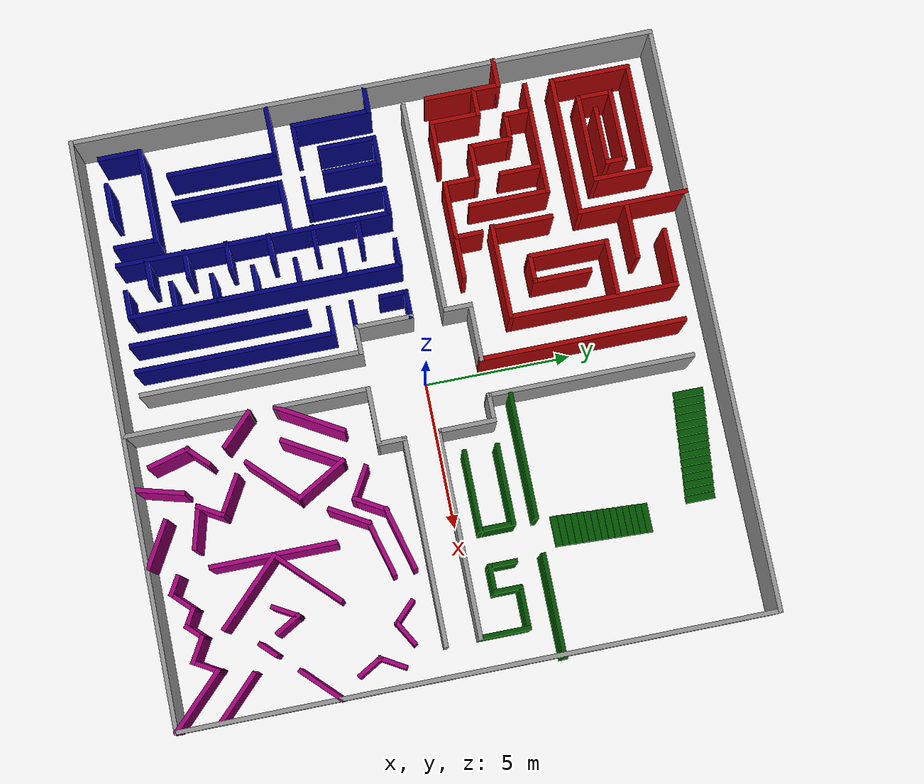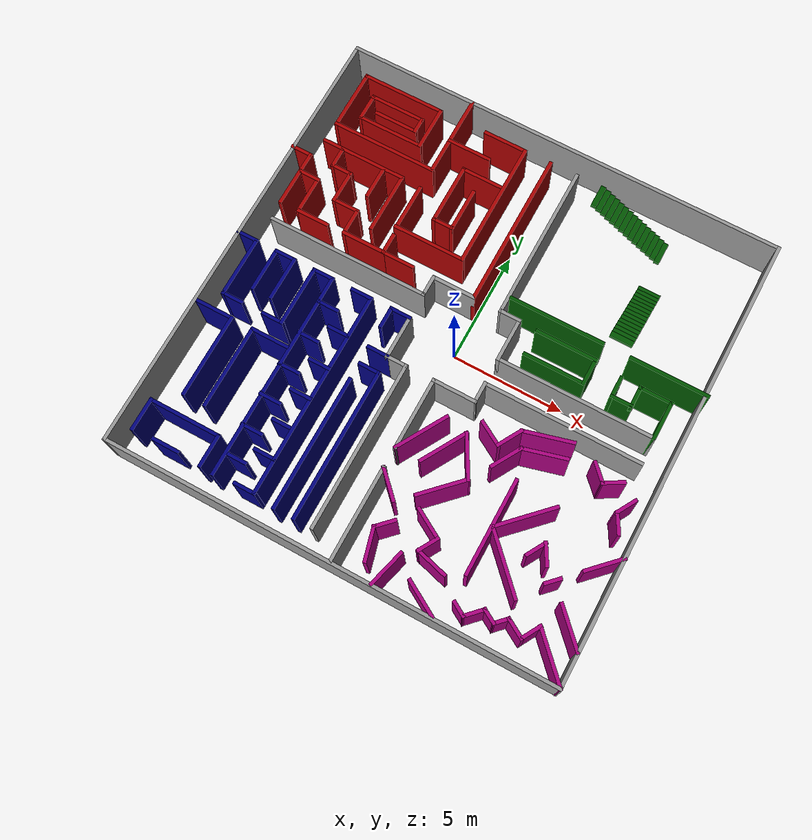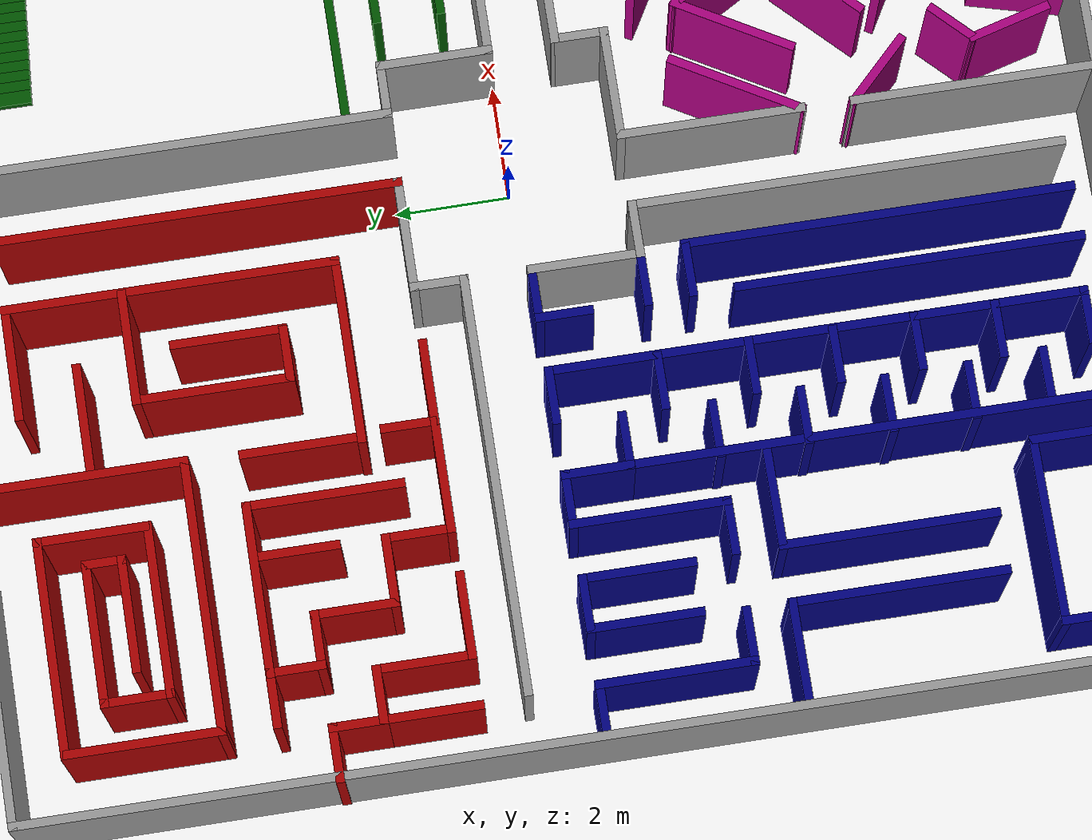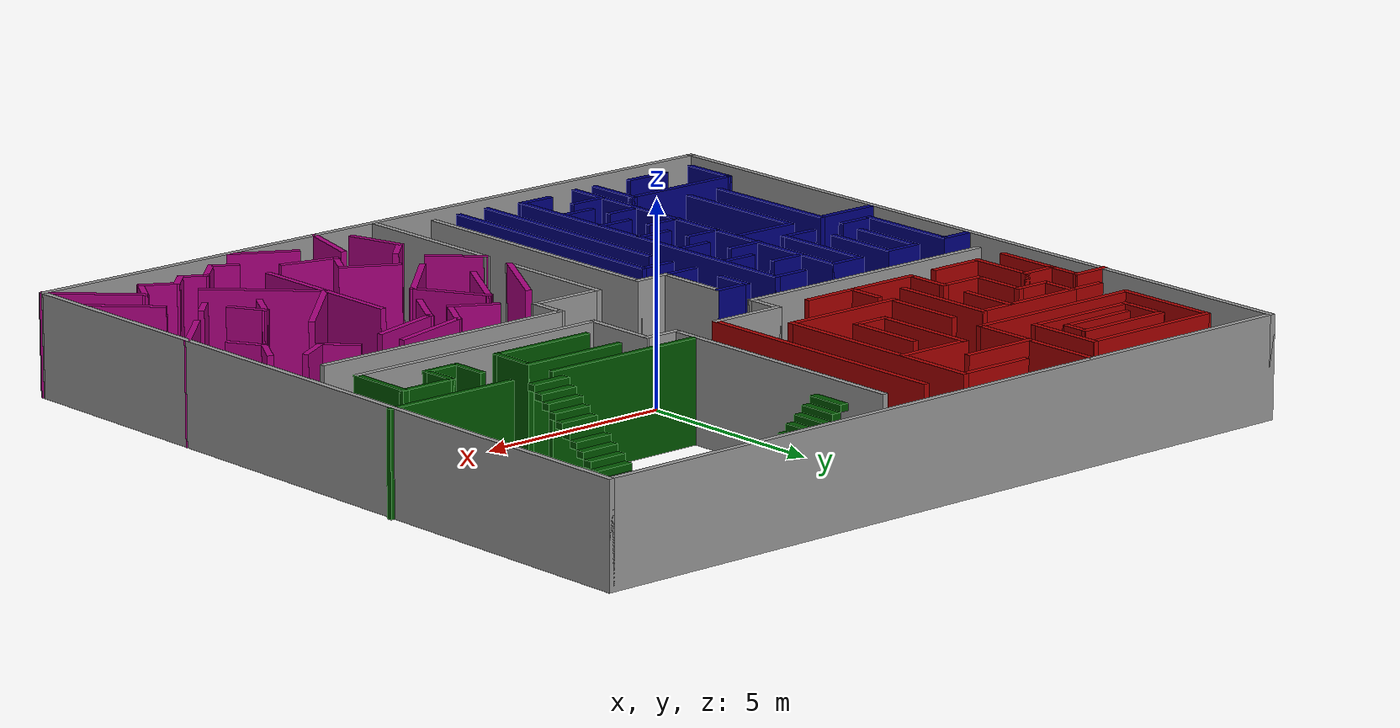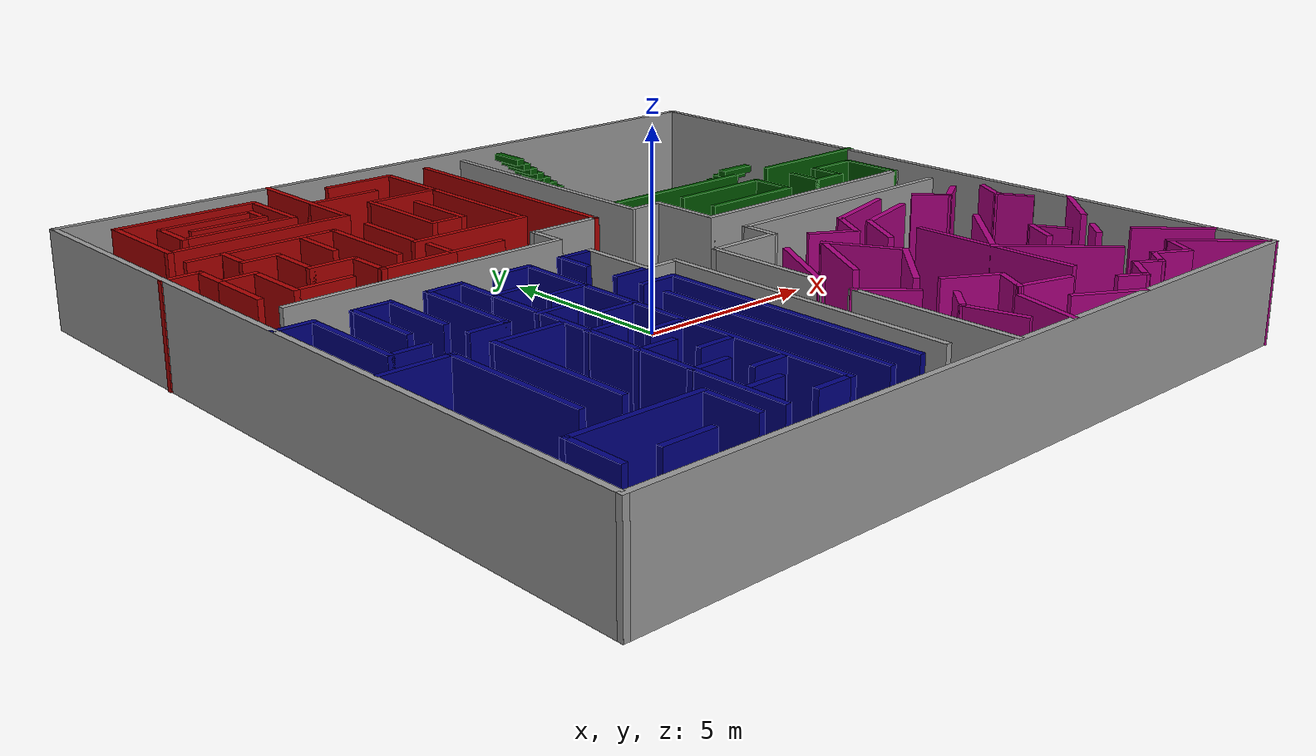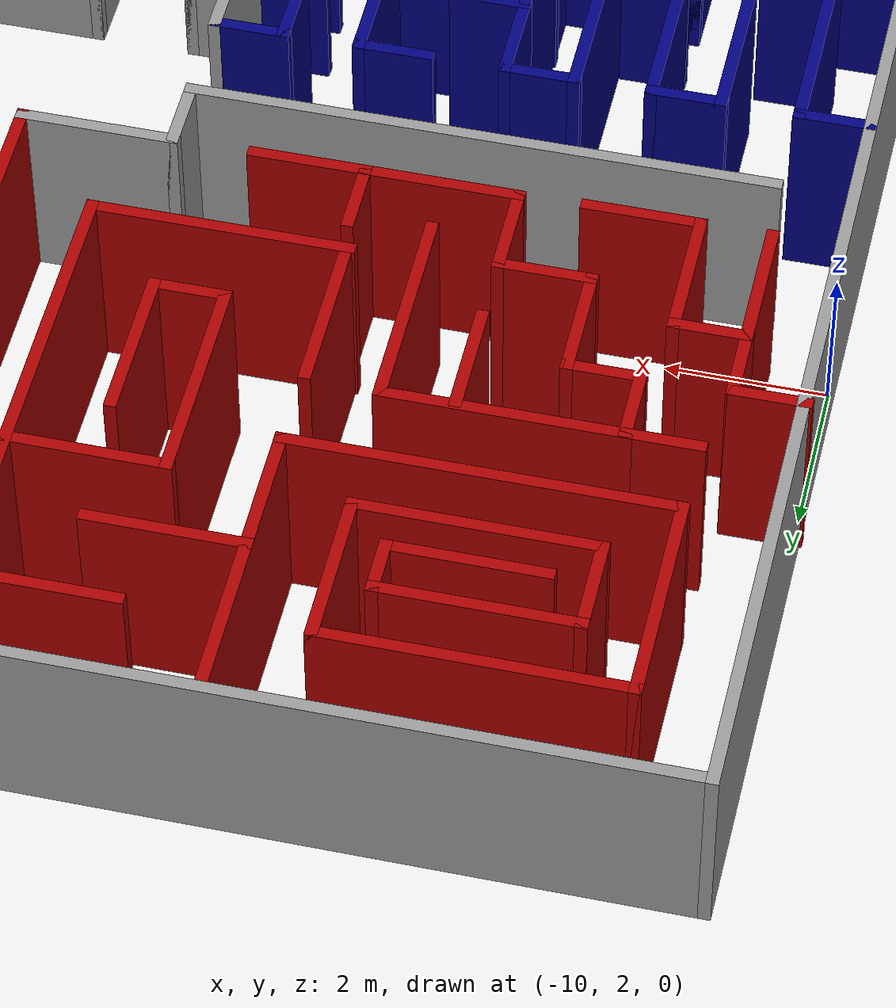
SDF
<?xml version='1.0'?>
<sdf version='1.7'>
  <model name='labyrinthe'>
    <pose>-0.042647 -0.217764 0 0 -0 0</pose>
    <link name='Stairs_0'>
      <visual name='Stairs_0_Visual_0'>
        <pose>5.96244 6.62392 0.083333 0 -0 0</pose>
        <geometry>
          <box>
            <size>1 0.233333 0.166667</size>
          </box>
        </geometry>
        <material>
          <script>
            <uri>file://media/materials/scripts/gazebo.material</uri>
            <name>Gazebo/Grey</name>
          </script>
          <ambient>0 0.333333 0 1</ambient>
        </material>
        <meta>
          <layer>0</layer>
        </meta>
      </visual>
      <collision name='Stairs_0_Collision_0'>
        <geometry>
          <box>
            <size>1 0.233333 0.166667</size>
          </box>
        </geometry>
        <pose>5.96244 6.62392 0.083333 0 -0 0</pose>
      </collision>
      <visual name='Stairs_0_Visual_1'>
        <pose>5.96244 6.39059 0.25 0 -0 0</pose>
        <geometry>
          <box>
            <size>1 0.233333 0.166667</size>
          </box>
        </geometry>
        <material>
          <script>
            <uri>file://media/materials/scripts/gazebo.material</uri>
            <name>Gazebo/Grey</name>
          </script>
          <ambient>0 0.333333 0 1</ambient>
        </material>
        <meta>
          <layer>0</layer>
        </meta>
      </visual>
      <collision name='Stairs_0_Collision_1'>
        <geometry>
          <box>
            <size>1 0.233333 0.166667</size>
          </box>
        </geometry>
        <pose>5.96244 6.39059 0.25 0 -0 0</pose>
      </collision>
      <visual name='Stairs_0_Visual_2'>
        <pose>5.96244 6.15725 0.416667 0 -0 0</pose>
        <geometry>
          <box>
            <size>1 0.233333 0.166667</size>
          </box>
        </geometry>
        <material>
          <script>
            <uri>file://media/materials/scripts/gazebo.material</uri>
            <name>Gazebo/Grey</name>
          </script>
          <ambient>0 0.333333 0 1</ambient>
        </material>
        <meta>
          <layer>0</layer>
        </meta>
      </visual>
      <collision name='Stairs_0_Collision_2'>
        <geometry>
          <box>
            <size>1 0.233333 0.166667</size>
          </box>
        </geometry>
        <pose>5.96244 6.15725 0.416667 0 -0 0</pose>
      </collision>
      <visual name='Stairs_0_Visual_3'>
        <pose>5.96244 5.92392 0.583333 0 -0 0</pose>
        <geometry>
          <box>
            <size>1 0.233333 0.166667</size>
          </box>
        </geometry>
        <material>
          <script>
            <uri>file://media/materials/scripts/gazebo.material</uri>
            <name>Gazebo/Grey</name>
          </script>
          <ambient>0 0.333333 0 1</ambient>
        </material>
        <meta>
          <layer>0</layer>
        </meta>
      </visual>
      <collision name='Stairs_0_Collision_3'>
        <geometry>
          <box>
            <size>1 0.233333 0.166667</size>
          </box>
        </geometry>
        <pose>5.96244 5.92392 0.583333 0 -0 0</pose>
      </collision>
      <visual name='Stairs_0_Visual_4'>
        <pose>5.96244 5.69059 0.75 0 -0 0</pose>
        <geometry>
          <box>
            <size>1 0.233333 0.166667</size>
          </box>
        </geometry>
        <material>
          <script>
            <uri>file://media/materials/scripts/gazebo.material</uri>
            <name>Gazebo/Grey</name>
          </script>
          <ambient>0 0.333333 0 1</ambient>
        </material>
        <meta>
          <layer>0</layer>
        </meta>
      </visual>
      <collision name='Stairs_0_Collision_4'>
        <geometry>
          <box>
            <size>1 0.233333 0.166667</size>
          </box>
        </geometry>
        <pose>5.96244 5.69059 0.75 0 -0 0</pose>
      </collision>
      <visual name='Stairs_0_Visual_5'>
        <pose>5.96244 5.45725 0.916667 0 -0 0</pose>
        <geometry>
          <box>
            <size>1 0.233333 0.166667</size>
          </box>
        </geometry>
        <material>
          <script>
            <uri>file://media/materials/scripts/gazebo.material</uri>
            <name>Gazebo/Grey</name>
          </script>
          <ambient>0 0.333333 0 1</ambient>
        </material>
        <meta>
          <layer>0</layer>
        </meta>
      </visual>
      <collision name='Stairs_0_Collision_5'>
        <geometry>
          <box>
            <size>1 0.233333 0.166667</size>
          </box>
        </geometry>
        <pose>5.96244 5.45725 0.916667 0 -0 0</pose>
      </collision>
      <visual name='Stairs_0_Visual_6'>
        <pose>5.96244 5.22392 1.08333 0 -0 0</pose>
        <geometry>
          <box>
            <size>1 0.233333 0.166667</size>
          </box>
        </geometry>
        <material>
          <script>
            <uri>file://media/materials/scripts/gazebo.material</uri>
            <name>Gazebo/Grey</name>
          </script>
          <ambient>0 0.333333 0 1</ambient>
        </material>
        <meta>
          <layer>0</layer>
        </meta>
      </visual>
      <collision name='Stairs_0_Collision_6'>
        <geometry>
          <box>
            <size>1 0.233333 0.166667</size>
          </box>
        </geometry>
        <pose>5.96244 5.22392 1.08333 0 -0 0</pose>
      </collision>
      <visual name='Stairs_0_Visual_7'>
        <pose>5.96244 4.99059 1.25 0 -0 0</pose>
        <geometry>
          <box>
            <size>1 0.233333 0.166667</size>
          </box>
        </geometry>
        <material>
          <script>
            <uri>file://media/materials/scripts/gazebo.material</uri>
            <name>Gazebo/Grey</name>
          </script>
          <ambient>0 0.333333 0 1</ambient>
        </material>
        <meta>
          <layer>0</layer>
        </meta>
      </visual>
      <collision name='Stairs_0_Collision_7'>
        <geometry>
          <box>
            <size>1 0.233333 0.166667</size>
          </box>
        </geometry>
        <pose>5.96244 4.99059 1.25 0 -0 0</pose>
      </collision>
      <visual name='Stairs_0_Visual_8'>
        <pose>5.96244 4.75725 1.41667 0 -0 0</pose>
        <geometry>
          <box>
            <size>1 0.233333 0.166667</size>
          </box>
        </geometry>
        <material>
          <script>
            <uri>file://media/materials/scripts/gazebo.material</uri>
            <name>Gazebo/Grey</name>
          </script>
          <ambient>0 0.333333 0 1</ambient>
        </material>
        <meta>
          <layer>0</layer>
        </meta>
      </visual>
      <collision name='Stairs_0_Collision_8'>
        <geometry>
          <box>
            <size>1 0.233333 0.166667</size>
          </box>
        </geometry>
        <pose>5.96244 4.75725 1.41667 0 -0 0</pose>
      </collision>
      <visual name='Stairs_0_Visual_9'>
        <pose>5.96244 4.52392 1.58333 0 -0 0</pose>
        <geometry>
          <box>
            <size>1 0.233333 0.166667</size>
          </box>
        </geometry>
        <material>
          <script>
            <uri>file://media/materials/scripts/gazebo.material</uri>
            <name>Gazebo/Grey</name>
          </script>
          <ambient>0 0.333333 0 1</ambient>
        </material>
        <meta>
          <layer>0</layer>
        </meta>
      </visual>
      <collision name='Stairs_0_Collision_9'>
        <geometry>
          <box>
            <size>1 0.233333 0.166667</size>
          </box>
        </geometry>
        <pose>5.96244 4.52392 1.58333 0 -0 0</pose>
      </collision>
      <visual name='Stairs_0_Visual_10'>
        <pose>5.96244 4.29059 1.75 0 -0 0</pose>
        <geometry>
          <box>
            <size>1 0.233333 0.166667</size>
          </box>
        </geometry>
        <material>
          <script>
            <uri>file://media/materials/scripts/gazebo.material</uri>
            <name>Gazebo/Grey</name>
          </script>
          <ambient>0 0.333333 0 1</ambient>
        </material>
        <meta>
          <layer>0</layer>
        </meta>
      </visual>
      <collision name='Stairs_0_Collision_10'>
        <geometry>
          <box>
            <size>1 0.233333 0.166667</size>
          </box>
        </geometry>
        <pose>5.96244 4.29059 1.75 0 -0 0</pose>
      </collision>
      <visual name='Stairs_0_Visual_11'>
        <pose>5.96244 4.05725 1.91667 0 -0 0</pose>
        <geometry>
          <box>
            <size>1 0.233333 0.166667</size>
          </box>
        </geometry>
        <material>
          <script>
            <uri>file://media/materials/scripts/gazebo.material</uri>
            <name>Gazebo/Grey</name>
          </script>
          <ambient>0 0.333333 0 1</ambient>
        </material>
        <meta>
          <layer>0</layer>
        </meta>
      </visual>
      <collision name='Stairs_0_Collision_11'>
        <geometry>
          <box>
            <size>1 0.233333 0.166667</size>
          </box>
        </geometry>
        <pose>5.96244 4.05725 1.91667 0 -0 0</pose>
      </collision>
      <visual name='Stairs_0_Visual_12'>
        <pose>5.96244 3.82392 2.08333 0 -0 0</pose>
        <geometry>
          <box>
            <size>1 0.233333 0.166667</size>
          </box>
        </geometry>
        <material>
          <script>
            <uri>file://media/materials/scripts/gazebo.material</uri>
            <name>Gazebo/Grey</name>
          </script>
          <ambient>0 0.333333 0 1</ambient>
        </material>
        <meta>
          <layer>0</layer>
        </meta>
      </visual>
      <collision name='Stairs_0_Collision_12'>
        <geometry>
          <box>
            <size>1 0.233333 0.166667</size>
          </box>
        </geometry>
        <pose>5.96244 3.82392 2.08333 0 -0 0</pose>
      </collision>
      <visual name='Stairs_0_Visual_13'>
        <pose>5.96244 3.59059 2.25 0 -0 0</pose>
        <geometry>
          <box>
            <size>1 0.233333 0.166667</size>
          </box>
        </geometry>
        <material>
          <script>
            <uri>file://media/materials/scripts/gazebo.material</uri>
            <name>Gazebo/Grey</name>
          </script>
          <ambient>0 0.333333 0 1</ambient>
        </material>
        <meta>
          <layer>0</layer>
        </meta>
      </visual>
      <collision name='Stairs_0_Collision_13'>
        <geometry>
          <box>
            <size>1 0.233333 0.166667</size>
          </box>
        </geometry>
        <pose>5.96244 3.59059 2.25 0 -0 0</pose>
      </collision>
      <visual name='Stairs_0_Visual_14'>
        <pose>5.96244 3.35725 2.41667 0 -0 0</pose>
        <geometry>
          <box>
            <size>1 0.233333 0.166667</size>
          </box>
        </geometry>
        <material>
          <script>
            <uri>file://media/materials/scripts/gazebo.material</uri>
            <name>Gazebo/Grey</name>
          </script>
          <ambient>0 0.333333 0 1</ambient>
        </material>
        <meta>
          <layer>0</layer>
        </meta>
      </visual>
      <collision name='Stairs_0_Collision_14'>
        <geometry>
          <box>
            <size>1 0.233333 0.166667</size>
          </box>
        </geometry>
        <pose>5.96244 3.35725 2.41667 0 -0 0</pose>
      </collision>
    </link>
    <link name='Stairs_1'>
      <visual name='Stairs_1_Visual_0'>
        <pose>5.63847 8.54811 0.083333 0 -0 -1.5708</pose>
        <geometry>
          <box>
            <size>1 0.233333 0.166667</size>
          </box>
        </geometry>
        <material>
          <script>
            <uri>file://media/materials/scripts/gazebo.material</uri>
            <name>Gazebo/Grey</name>
          </script>
          <ambient>0 0.333333 0 1</ambient>
        </material>
        <meta>
          <layer>0</layer>
        </meta>
      </visual>
      <collision name='Stairs_1_Collision_0'>
        <geometry>
          <box>
            <size>1 0.233333 0.166667</size>
          </box>
        </geometry>
        <pose>5.63847 8.54811 0.083333 0 -0 -1.5708</pose>
      </collision>
      <visual name='Stairs_1_Visual_1'>
        <pose>5.40514 8.54811 0.25 0 -0 -1.5708</pose>
        <geometry>
          <box>
            <size>1 0.233333 0.166667</size>
          </box>
        </geometry>
        <material>
          <script>
            <uri>file://media/materials/scripts/gazebo.material</uri>
            <name>Gazebo/Grey</name>
          </script>
          <ambient>0 0.333333 0 1</ambient>
        </material>
        <meta>
          <layer>0</layer>
        </meta>
      </visual>
      <collision name='Stairs_1_Collision_1'>
        <geometry>
          <box>
            <size>1 0.233333 0.166667</size>
          </box>
        </geometry>
        <pose>5.40514 8.54811 0.25 0 -0 -1.5708</pose>
      </collision>
      <visual name='Stairs_1_Visual_2'>
        <pose>5.1718 8.54811 0.416667 0 -0 -1.5708</pose>
        <geometry>
          <box>
            <size>1 0.233333 0.166667</size>
          </box>
        </geometry>
        <material>
          <script>
            <uri>file://media/materials/scripts/gazebo.material</uri>
            <name>Gazebo/Grey</name>
          </script>
          <ambient>0 0.333333 0 1</ambient>
        </material>
        <meta>
          <layer>0</layer>
        </meta>
      </visual>
      <collision name='Stairs_1_Collision_2'>
        <geometry>
          <box>
            <size>1 0.233333 0.166667</size>
          </box>
        </geometry>
        <pose>5.1718 8.54811 0.416667 0 -0 -1.5708</pose>
      </collision>
      <visual name='Stairs_1_Visual_3'>
        <pose>4.93847 8.54811 0.583333 0 -0 -1.5708</pose>
        <geometry>
          <box>
            <size>1 0.233333 0.166667</size>
          </box>
        </geometry>
        <material>
          <script>
            <uri>file://media/materials/scripts/gazebo.material</uri>
            <name>Gazebo/Grey</name>
          </script>
          <ambient>0 0.333333 0 1</ambient>
        </material>
        <meta>
          <layer>0</layer>
        </meta>
      </visual>
      <collision name='Stairs_1_Collision_3'>
        <geometry>
          <box>
            <size>1 0.233333 0.166667</size>
          </box>
        </geometry>
        <pose>4.93847 8.54811 0.583333 0 -0 -1.5708</pose>
      </collision>
      <visual name='Stairs_1_Visual_4'>
        <pose>4.70514 8.54811 0.75 0 -0 -1.5708</pose>
        <geometry>
          <box>
            <size>1 0.233333 0.166667</size>
          </box>
        </geometry>
        <material>
          <script>
            <uri>file://media/materials/scripts/gazebo.material</uri>
            <name>Gazebo/Grey</name>
          </script>
          <ambient>0 0.333333 0 1</ambient>
        </material>
        <meta>
          <layer>0</layer>
        </meta>
      </visual>
      <collision name='Stairs_1_Collision_4'>
        <geometry>
          <box>
            <size>1 0.233333 0.166667</size>
          </box>
        </geometry>
        <pose>4.70514 8.54811 0.75 0 -0 -1.5708</pose>
      </collision>
      <visual name='Stairs_1_Visual_5'>
        <pose>4.4718 8.54811 0.916667 0 -0 -1.5708</pose>
        <geometry>
          <box>
            <size>1 0.233333 0.166667</size>
          </box>
        </geometry>
        <material>
          <script>
            <uri>file://media/materials/scripts/gazebo.material</uri>
            <name>Gazebo/Grey</name>
          </script>
          <ambient>0 0.333333 0 1</ambient>
        </material>
        <meta>
          <layer>0</layer>
        </meta>
      </visual>
      <collision name='Stairs_1_Collision_5'>
        <geometry>
          <box>
            <size>1 0.233333 0.166667</size>
          </box>
        </geometry>
        <pose>4.4718 8.54811 0.916667 0 -0 -1.5708</pose>
      </collision>
      <visual name='Stairs_1_Visual_6'>
        <pose>4.23847 8.54811 1.08333 0 -0 -1.5708</pose>
        <geometry>
          <box>
            <size>1 0.233333 0.166667</size>
          </box>
        </geometry>
        <material>
          <script>
            <uri>file://media/materials/scripts/gazebo.material</uri>
            <name>Gazebo/Grey</name>
          </script>
          <ambient>0 0.333333 0 1</ambient>
        </material>
        <meta>
          <layer>0</layer>
        </meta>
      </visual>
      <collision name='Stairs_1_Collision_6'>
        <geometry>
          <box>
            <size>1 0.233333 0.166667</size>
          </box>
        </geometry>
        <pose>4.23847 8.54811 1.08333 0 -0 -1.5708</pose>
      </collision>
      <visual name='Stairs_1_Visual_7'>
        <pose>4.00514 8.54811 1.25 0 -0 -1.5708</pose>
        <geometry>
          <box>
            <size>1 0.233333 0.166667</size>
          </box>
        </geometry>
        <material>
          <script>
            <uri>file://media/materials/scripts/gazebo.material</uri>
            <name>Gazebo/Grey</name>
          </script>
          <ambient>0 0.333333 0 1</ambient>
        </material>
        <meta>
          <layer>0</layer>
        </meta>
      </visual>
      <collision name='Stairs_1_Collision_7'>
        <geometry>
          <box>
            <size>1 0.233333 0.166667</size>
          </box>
        </geometry>
        <pose>4.00514 8.54811 1.25 0 -0 -1.5708</pose>
      </collision>
      <visual name='Stairs_1_Visual_8'>
        <pose>3.77181 8.54811 1.41667 0 -0 -1.5708</pose>
        <geometry>
          <box>
            <size>1 0.233333 0.166667</size>
          </box>
        </geometry>
        <material>
          <script>
            <uri>file://media/materials/scripts/gazebo.material</uri>
            <name>Gazebo/Grey</name>
          </script>
          <ambient>0 0.333333 0 1</ambient>
        </material>
        <meta>
          <layer>0</layer>
        </meta>
      </visual>
      <collision name='Stairs_1_Collision_8'>
        <geometry>
          <box>
            <size>1 0.233333 0.166667</size>
          </box>
        </geometry>
        <pose>3.77181 8.54811 1.41667 0 -0 -1.5708</pose>
      </collision>
      <visual name='Stairs_1_Visual_9'>
        <pose>3.53847 8.54811 1.58333 0 -0 -1.5708</pose>
        <geometry>
          <box>
            <size>1 0.233333 0.166667</size>
          </box>
        </geometry>
        <material>
          <script>
            <uri>file://media/materials/scripts/gazebo.material</uri>
            <name>Gazebo/Grey</name>
          </script>
          <ambient>0 0.333333 0 1</ambient>
        </material>
        <meta>
          <layer>0</layer>
        </meta>
      </visual>
      <collision name='Stairs_1_Collision_9'>
        <geometry>
          <box>
            <size>1 0.233333 0.166667</size>
          </box>
        </geometry>
        <pose>3.53847 8.54811 1.58333 0 -0 -1.5708</pose>
      </collision>
      <visual name='Stairs_1_Visual_10'>
        <pose>3.30514 8.54811 1.75 0 -0 -1.5708</pose>
        <geometry>
          <box>
            <size>1 0.233333 0.166667</size>
          </box>
        </geometry>
        <material>
          <script>
            <uri>file://media/materials/scripts/gazebo.material</uri>
            <name>Gazebo/Grey</name>
          </script>
          <ambient>0 0.333333 0 1</ambient>
        </material>
        <meta>
          <layer>0</layer>
        </meta>
      </visual>
      <collision name='Stairs_1_Collision_10'>
        <geometry>
          <box>
            <size>1 0.233333 0.166667</size>
          </box>
        </geometry>
        <pose>3.30514 8.54811 1.75 0 -0 -1.5708</pose>
      </collision>
      <visual name='Stairs_1_Visual_11'>
        <pose>3.0718 8.54811 1.91667 0 -0 -1.5708</pose>
        <geometry>
          <box>
            <size>1 0.233333 0.166667</size>
          </box>
        </geometry>
        <material>
          <script>
            <uri>file://media/materials/scripts/gazebo.material</uri>
            <name>Gazebo/Grey</name>
          </script>
          <ambient>0 0.333333 0 1</ambient>
        </material>
        <meta>
          <layer>0</layer>
        </meta>
      </visual>
      <collision name='Stairs_1_Collision_11'>
        <geometry>
          <box>
            <size>1 0.233333 0.166667</size>
          </box>
        </geometry>
        <pose>3.0718 8.54811 1.91667 0 -0 -1.5708</pose>
      </collision>
      <visual name='Stairs_1_Visual_12'>
        <pose>2.83847 8.54811 2.08333 0 -0 -1.5708</pose>
        <geometry>
          <box>
            <size>1 0.233333 0.166667</size>
          </box>
        </geometry>
        <material>
          <script>
            <uri>file://media/materials/scripts/gazebo.material</uri>
            <name>Gazebo/Grey</name>
          </script>
          <ambient>0 0.333333 0 1</ambient>
        </material>
        <meta>
          <layer>0</layer>
        </meta>
      </visual>
      <collision name='Stairs_1_Collision_12'>
        <geometry>
          <box>
            <size>1 0.233333 0.166667</size>
          </box>
        </geometry>
        <pose>2.83847 8.54811 2.08333 0 -0 -1.5708</pose>
      </collision>
      <visual name='Stairs_1_Visual_13'>
        <pose>2.60514 8.54811 2.25 0 -0 -1.5708</pose>
        <geometry>
          <box>
            <size>1 0.233333 0.166667</size>
          </box>
        </geometry>
        <material>
          <script>
            <uri>file://media/materials/scripts/gazebo.material</uri>
            <name>Gazebo/Grey</name>
          </script>
          <ambient>0 0.333333 0 1</ambient>
        </material>
        <meta>
          <layer>0</layer>
        </meta>
      </visual>
      <collision name='Stairs_1_Collision_13'>
        <geometry>
          <box>
            <size>1 0.233333 0.166667</size>
          </box>
        </geometry>
        <pose>2.60514 8.54811 2.25 0 -0 -1.5708</pose>
      </collision>
      <visual name='Stairs_1_Visual_14'>
        <pose>2.3718 8.54811 2.41667 0 -0 -1.5708</pose>
        <geometry>
          <box>
            <size>1 0.233333 0.166667</size>
          </box>
        </geometry>
        <material>
          <script>
            <uri>file://media/materials/scripts/gazebo.material</uri>
            <name>Gazebo/Grey</name>
          </script>
          <ambient>0 0.333333 0 1</ambient>
        </material>
        <meta>
          <layer>0</layer>
        </meta>
      </visual>
      <collision name='Stairs_1_Collision_14'>
        <geometry>
          <box>
            <size>1 0.233333 0.166667</size>
          </box>
        </geometry>
        <pose>2.3718 8.54811 2.41667 0 -0 -1.5708</pose>
      </collision>
    </link>
    <link name='Wall_100'>
      <collision name='Wall_100_Collision'>
        <geometry>
          <box>
            <size>1 0.15 2.5</size>
          </box>
        </geometry>
        <pose>0 0 1.25 0 -0 0</pose>
      </collision>
      <visual name='Wall_100_Visual'>
        <pose>0 0 1.25 0 -0 0</pose>
        <geometry>
          <box>
            <size>1 0.15 2.5</size>
          </box>
        </geometry>
        <material>
          <script>
            <uri>file://media/materials/scripts/gazebo.material</uri>
            <name>Gazebo/Grey</name>
          </script>
          <ambient>0.666667 0 0 1</ambient>
        </material>
        <meta>
          <layer>0</layer>
        </meta>
      </visual>
      <pose>-4.27476 2.53254 0 0 -0 1.5708</pose>
    </link>
    <link name='Wall_102'>
      <collision name='Wall_102_Collision'>
        <geometry>
          <box>
            <size>2 0.15 2.5</size>
          </box>
        </geometry>
        <pose>0 0 1.25 0 -0 0</pose>
      </collision>
      <visual name='Wall_102_Visual'>
        <pose>0 0 1.25 0 -0 0</pose>
        <geometry>
          <box>
            <size>2 0.15 2.5</size>
          </box>
        </geometry>
        <material>
          <script>
            <uri>file://media/materials/scripts/gazebo.material</uri>
            <name>Gazebo/Grey</name>
          </script>
          <ambient>0.666667 0 0 1</ambient>
        </material>
        <meta>
          <layer>0</layer>
        </meta>
      </visual>
      <pose>-5.19976 2.10754 0 0 -0 3.14159</pose>
    </link>
    <link name='Wall_103'>
      <collision name='Wall_103_Collision'>
        <geometry>
          <box>
            <size>1.25 0.15 2.5</size>
          </box>
        </geometry>
        <pose>0 0 1.25 0 -0 0</pose>
      </collision>
      <visual name='Wall_103_Visual'>
        <pose>0 0 1.25 0 -0 0</pose>
        <geometry>
          <box>
            <size>1.25 0.15 2.5</size>
          </box>
        </geometry>
        <material>
          <script>
            <uri>file://media/materials/scripts/gazebo.material</uri>
            <name>Gazebo/Grey</name>
          </script>
          <ambient>0.666667 0 0 1</ambient>
        </material>
        <meta>
          <layer>0</layer>
        </meta>
      </visual>
      <pose>-6.12476 2.65754 0 0 -0 1.5708</pose>
    </link>
    <link name='Wall_104'>
      <collision name='Wall_104_Collision'>
        <geometry>
          <box>
            <size>1.25 0.15 2.5</size>
          </box>
        </geometry>
        <pose>0 0 1.25 0 -0 0</pose>
      </collision>
      <visual name='Wall_104_Visual'>
        <pose>0 0 1.25 0 -0 0</pose>
        <geometry>
          <box>
            <size>1.25 0.15 2.5</size>
          </box>
        </geometry>
        <material>
          <script>
            <uri>file://media/materials/scripts/gazebo.material</uri>
            <name>Gazebo/Grey</name>
          </script>
          <ambient>0.666667 0 0 1</ambient>
        </material>
        <meta>
          <layer>0</layer>
        </meta>
      </visual>
      <pose>-6.67476 3.20754 0 0 -0 3.14159</pose>
    </link>
    <link name='Wall_105'>
      <collision name='Wall_105_Collision'>
        <geometry>
          <box>
            <size>1.5 0.15 2.5</size>
          </box>
        </geometry>
        <pose>0 0 1.25 0 -0 0</pose>
      </collision>
      <visual name='Wall_105_Visual'>
        <pose>0 0 1.25 0 -0 0</pose>
        <geometry>
          <box>
            <size>1.5 0.15 2.5</size>
          </box>
        </geometry>
        <material>
          <script>
            <uri>file://media/materials/scripts/gazebo.material</uri>
            <name>Gazebo/Grey</name>
          </script>
          <ambient>0.666667 0 0 1</ambient>
        </material>
        <meta>
          <layer>0</layer>
        </meta>
      </visual>
      <pose>-7.22476 3.88254 0 0 -0 1.5708</pose>
    </link>
    <link name='Wall_106'>
      <collision name='Wall_106_Collision'>
        <geometry>
          <box>
            <size>1 0.15 2.5</size>
          </box>
        </geometry>
        <pose>0 0 1.25 0 -0 0</pose>
      </collision>
      <visual name='Wall_106_Visual'>
        <pose>0 0 1.25 0 -0 0</pose>
        <geometry>
          <box>
            <size>1 0.15 2.5</size>
          </box>
        </geometry>
        <material>
          <script>
            <uri>file://media/materials/scripts/gazebo.material</uri>
            <name>Gazebo/Grey</name>
          </script>
          <ambient>0.666667 0 0 1</ambient>
        </material>
        <meta>
          <layer>0</layer>
        </meta>
      </visual>
      <pose>-7.64976 4.55754 0 0 -0 3.14159</pose>
    </link>
    <link name='Wall_107'>
      <collision name='Wall_107_Collision'>
        <geometry>
          <box>
            <size>1 0.15 2.5</size>
          </box>
        </geometry>
        <pose>0 0 1.25 0 -0 0</pose>
      </collision>
      <visual name='Wall_107_Visual'>
        <pose>0 0 1.25 0 -0 0</pose>
        <geometry>
          <box>
            <size>1 0.15 2.5</size>
          </box>
        </geometry>
        <material>
          <script>
            <uri>file://media/materials/scripts/gazebo.material</uri>
            <name>Gazebo/Grey</name>
          </script>
          <ambient>0.666667 0 0 1</ambient>
        </material>
        <meta>
          <layer>0</layer>
        </meta>
      </visual>
      <pose>-8.07476 4.98254 0 0 -0 1.5708</pose>
    </link>
    <link name='Wall_108'>
      <collision name='Wall_108_Collision'>
        <geometry>
          <box>
            <size>1 0.15 2.5</size>
          </box>
        </geometry>
        <pose>0 0 1.25 0 -0 0</pose>
      </collision>
      <visual name='Wall_108_Visual'>
        <pose>0 0 1.25 0 -0 0</pose>
        <geometry>
          <box>
            <size>1 0.15 2.5</size>
          </box>
        </geometry>
        <material>
          <script>
            <uri>file://media/materials/scripts/gazebo.material</uri>
            <name>Gazebo/Grey</name>
          </script>
          <ambient>0.666667 0 0 1</ambient>
        </material>
        <meta>
          <layer>0</layer>
        </meta>
      </visual>
      <pose>-8.51299 5.42076 0 0 -0 3.14159</pose>
    </link>
    <link name='Wall_110'>
      <collision name='Wall_110_Collision'>
        <geometry>
          <box>
            <size>1 0.15 2.5</size>
          </box>
        </geometry>
        <pose>0 0 1.25 0 -0 0</pose>
      </collision>
      <visual name='Wall_110_Visual'>
        <pose>0 0 1.25 0 -0 0</pose>
        <geometry>
          <box>
            <size>1 0.15 2.5</size>
          </box>
        </geometry>
        <material>
          <script>
            <uri>file://media/materials/scripts/gazebo.material</uri>
            <name>Gazebo/Grey</name>
          </script>
          <ambient>0.666667 0 0 1</ambient>
        </material>
        <meta>
          <layer>0</layer>
        </meta>
      </visual>
      <pose>-9.56191 4.52771 0 0 -0 0</pose>
    </link>
    <link name='Wall_111'>
      <collision name='Wall_111_Collision'>
        <geometry>
          <box>
            <size>1 0.15 2.5</size>
          </box>
        </geometry>
        <pose>0 0 1.25 0 -0 0</pose>
      </collision>
      <visual name='Wall_111_Visual'>
        <pose>0 0 1.25 0 -0 0</pose>
        <geometry>
          <box>
            <size>1 0.15 2.5</size>
          </box>
        </geometry>
        <material>
          <script>
            <uri>file://media/materials/scripts/gazebo.material</uri>
            <name>Gazebo/Grey</name>
          </script>
          <ambient>0.666667 0 0 1</ambient>
        </material>
        <meta>
          <layer>0</layer>
        </meta>
      </visual>
      <pose>-9.13691 4.10271 0 0 -0 -1.5708</pose>
    </link>
    <link name='Wall_112'>
      <collision name='Wall_112_Collision'>
        <geometry>
          <box>
            <size>1 0.15 2.5</size>
          </box>
        </geometry>
        <pose>0 0 1.25 0 -0 0</pose>
      </collision>
      <visual name='Wall_112_Visual'>
        <pose>0 0 1.25 0 -0 0</pose>
        <geometry>
          <box>
            <size>1 0.15 2.5</size>
          </box>
        </geometry>
        <material>
          <script>
            <uri>file://media/materials/scripts/gazebo.material</uri>
            <name>Gazebo/Grey</name>
          </script>
          <ambient>0.666667 0 0 1</ambient>
        </material>
        <meta>
          <layer>0</layer>
        </meta>
      </visual>
      <pose>-8.71191 3.67771 0 0 -0 0</pose>
    </link>
    <link name='Wall_113'>
      <collision name='Wall_113_Collision'>
        <geometry>
          <box>
            <size>1.75 0.15 2.5</size>
          </box>
        </geometry>
        <pose>0 0 1.25 0 -0 0</pose>
      </collision>
      <visual name='Wall_113_Visual'>
        <pose>0 0 1.25 0 -0 0</pose>
        <geometry>
          <box>
            <size>1.75 0.15 2.5</size>
          </box>
        </geometry>
        <material>
          <script>
            <uri>file://media/materials/scripts/gazebo.material</uri>
            <name>Gazebo/Grey</name>
          </script>
          <ambient>0.666667 0 0 1</ambient>
        </material>
        <meta>
          <layer>0</layer>
        </meta>
      </visual>
      <pose>-8.28691 2.87771 0 0 -0 -1.5708</pose>
    </link>
    <link name='Wall_114'>
      <collision name='Wall_114_Collision'>
        <geometry>
          <box>
            <size>1.5 0.15 2.5</size>
          </box>
        </geometry>
        <pose>0 0 1.25 0 -0 0</pose>
      </collision>
      <visual name='Wall_114_Visual'>
        <pose>0 0 1.25 0 -0 0</pose>
        <geometry>
          <box>
            <size>1.5 0.15 2.5</size>
          </box>
        </geometry>
        <material>
          <script>
            <uri>file://media/materials/scripts/gazebo.material</uri>
            <name>Gazebo/Grey</name>
          </script>
          <ambient>0.666667 0 0 1</ambient>
        </material>
        <meta>
          <layer>0</layer>
        </meta>
      </visual>
      <pose>-7.61191 2.07771 0 0 -0 0</pose>
    </link>
    <link name='Wall_116'>
      <collision name='Wall_116_Collision'>
        <geometry>
          <box>
            <size>1.75 0.15 2.5</size>
          </box>
        </geometry>
        <pose>0 0 1.25 0 -0 0</pose>
      </collision>
      <visual name='Wall_116_Visual'>
        <pose>0 0 1.25 0 -0 0</pose>
        <geometry>
          <box>
            <size>1.75 0.15 2.5</size>
          </box>
        </geometry>
        <material>
          <script>
            <uri>file://media/materials/scripts/gazebo.material</uri>
            <name>Gazebo/Grey</name>
          </script>
          <ambient>0.666667 0 0 1</ambient>
        </material>
        <meta>
          <layer>0</layer>
        </meta>
      </visual>
      <pose>-9.13691 2.87771 0 0 -0 -1.5708</pose>
    </link>
    <link name='Wall_118'>
      <collision name='Wall_118_Collision'>
        <geometry>
          <box>
            <size>3 0.15 2.5</size>
          </box>
        </geometry>
        <pose>0 0 1.25 0 -0 0</pose>
      </collision>
      <visual name='Wall_118_Visual'>
        <pose>0 0 1.25 0 -0 0</pose>
        <geometry>
          <box>
            <size>3 0.15 2.5</size>
          </box>
        </geometry>
        <material>
          <script>
            <uri>file://media/materials/scripts/gazebo.material</uri>
            <name>Gazebo/Grey</name>
          </script>
          <ambient>0.666667 0 0 1</ambient>
        </material>
        <meta>
          <layer>0</layer>
        </meta>
      </visual>
      <pose>-6.66299 5.42076 0 0 -0 0</pose>
    </link>
    <link name='Wall_119'>
      <collision name='Wall_119_Collision'>
        <geometry>
          <box>
            <size>2.75 0.15 2.5</size>
          </box>
        </geometry>
        <pose>0 0 1.25 0 -0 0</pose>
      </collision>
      <visual name='Wall_119_Visual'>
        <pose>0 0 1.25 0 -0 0</pose>
        <geometry>
          <box>
            <size>2.75 0.15 2.5</size>
          </box>
        </geometry>
        <material>
          <script>
            <uri>file://media/materials/scripts/gazebo.material</uri>
            <name>Gazebo/Grey</name>
          </script>
          <ambient>0.666667 0 0 1</ambient>
        </material>
        <meta>
          <layer>0</layer>
        </meta>
      </visual>
      <pose>-5.23799 4.12076 0 0 -0 -1.5708</pose>
    </link>
    <link name='Wall_121'>
      <collision name='Wall_121_Collision'>
        <geometry>
          <box>
            <size>1.5 0.15 2.5</size>
          </box>
        </geometry>
        <pose>0 0 1.25 0 -0 0</pose>
      </collision>
      <visual name='Wall_121_Visual'>
        <pose>0 0 1.25 0 -0 0</pose>
        <geometry>
          <box>
            <size>1.5 0.15 2.5</size>
          </box>
        </geometry>
        <material>
          <script>
            <uri>file://media/materials/scripts/gazebo.material</uri>
            <name>Gazebo/Grey</name>
          </script>
          <ambient>0.666667 0 0 1</ambient>
        </material>
        <meta>
          <layer>0</layer>
        </meta>
      </visual>
      <pose>-6.11199 4.71234 0 0 -0 -1.5708</pose>
    </link>
    <link name='Wall_123'>
      <collision name='Wall_123_Collision'>
        <geometry>
          <box>
            <size>1 0.15 2.5</size>
          </box>
        </geometry>
        <pose>0 0 1.25 0 -0 0</pose>
      </collision>
      <visual name='Wall_123_Visual'>
        <pose>0 0 1.25 0 -0 0</pose>
        <geometry>
          <box>
            <size>1 0.15 2.5</size>
          </box>
        </geometry>
        <material>
          <script>
            <uri>file://media/materials/scripts/gazebo.material</uri>
            <name>Gazebo/Grey</name>
          </script>
          <ambient>0 0 0.498039 1</ambient>
        </material>
        <meta>
          <layer>0</layer>
        </meta>
      </visual>
      <pose>-2.35877 0.113732 0 0 -0 3.14159</pose>
    </link>
    <link name='Wall_124'>
      <collision name='Wall_124_Collision'>
        <geometry>
          <box>
            <size>1 0.15 2.5</size>
          </box>
        </geometry>
        <pose>0 0 1.25 0 -0 0</pose>
      </collision>
      <visual name='Wall_124_Visual'>
        <pose>0 0 1.25 0 -0 0</pose>
        <geometry>
          <box>
            <size>1 0.15 2.5</size>
          </box>
        </geometry>
        <material>
          <script>
            <uri>file://media/materials/scripts/gazebo.material</uri>
            <name>Gazebo/Grey</name>
          </script>
          <ambient>0 0 0.498039 1</ambient>
        </material>
        <meta>
          <layer>0</layer>
        </meta>
      </visual>
      <pose>-2.78376 -0.311268 0 0 -0 -1.5708</pose>
    </link>
    <link name='Wall_126'>
      <collision name='Wall_126_Collision'>
        <geometry>
          <box>
            <size>1 0.15 2.5</size>
          </box>
        </geometry>
        <pose>0 0 1.25 0 -0 0</pose>
      </collision>
      <visual name='Wall_126_Visual'>
        <pose>0 0 1.25 0 -0 0</pose>
        <geometry>
          <box>
            <size>1 0.15 2.5</size>
          </box>
        </geometry>
        <material>
          <script>
            <uri>file://media/materials/scripts/gazebo.material</uri>
            <name>Gazebo/Grey</name>
          </script>
          <ambient>0 0 0.498039 1</ambient>
        </material>
        <meta>
          <layer>0</layer>
        </meta>
      </visual>
      <pose>-4.14326 0.097337 0 0 -0 3.14159</pose>
    </link>
    <link name='Wall_128'>
      <collision name='Wall_128_Collision'>
        <geometry>
          <box>
            <size>1 0.15 2.5</size>
          </box>
        </geometry>
        <pose>0 0 1.25 0 -0 0</pose>
      </collision>
      <visual name='Wall_128_Visual'>
        <pose>0 0 1.25 0 -0 0</pose>
        <geometry>
          <box>
            <size>1 0.15 2.5</size>
          </box>
        </geometry>
        <material>
          <script>
            <uri>file://media/materials/scripts/gazebo.material</uri>
            <name>Gazebo/Grey</name>
          </script>
          <ambient>0 0 0.498039 1</ambient>
        </material>
        <meta>
          <layer>0</layer>
        </meta>
      </visual>
      <pose>-5.94186 0.097337 0 0 -0 3.14159</pose>
    </link>
    <link name='Wall_130'>
      <collision name='Wall_130_Collision'>
        <geometry>
          <box>
            <size>1 0.15 2.5</size>
          </box>
        </geometry>
        <pose>0 0 1.25 0 -0 0</pose>
      </collision>
      <visual name='Wall_130_Visual'>
        <pose>0 0 1.25 0 -0 0</pose>
        <geometry>
          <box>
            <size>1 0.15 2.5</size>
          </box>
        </geometry>
        <material>
          <script>
            <uri>file://media/materials/scripts/gazebo.material</uri>
            <name>Gazebo/Grey</name>
          </script>
          <ambient>0 0 0.498039 1</ambient>
        </material>
        <meta>
          <layer>0</layer>
        </meta>
      </visual>
      <pose>-7.72724 0.084112 0 0 -0 3.14159</pose>
    </link>
    <link name='Wall_132'>
      <collision name='Wall_132_Collision'>
        <geometry>
          <box>
            <size>1 0.15 2.5</size>
          </box>
        </geometry>
        <pose>0 0 1.25 0 -0 0</pose>
      </collision>
      <visual name='Wall_132_Visual'>
        <pose>0 0 1.25 0 -0 0</pose>
        <geometry>
          <box>
            <size>1 0.15 2.5</size>
          </box>
        </geometry>
        <material>
          <script>
            <uri>file://media/materials/scripts/gazebo.material</uri>
            <name>Gazebo/Grey</name>
          </script>
          <ambient>0 0 0.498039 1</ambient>
        </material>
        <meta>
          <layer>0</layer>
        </meta>
      </visual>
      <pose>-9.52224 0.084112 0 0 -0 0</pose>
    </link>
    <link name='Wall_134'>
      <collision name='Wall_134_Collision'>
        <geometry>
          <box>
            <size>9.25 0.15 2.5</size>
          </box>
        </geometry>
        <pose>0 0 1.25 0 -0 0</pose>
      </collision>
      <visual name='Wall_134_Visual'>
        <pose>0 0 1.25 0 -0 0</pose>
        <geometry>
          <box>
            <size>9.25 0.15 2.5</size>
          </box>
        </geometry>
        <material>
          <script>
            <uri>file://media/materials/scripts/gazebo.material</uri>
            <name>Gazebo/Grey</name>
          </script>
          <ambient>0 0 0.498039 1</ambient>
        </material>
        <meta>
          <layer>0</layer>
        </meta>
      </visual>
      <pose>-3.71826 -4.45266 0 0 -0 -1.5708</pose>
    </link>
    <link name='Wall_138'>
      <collision name='Wall_138_Collision'>
        <geometry>
          <box>
            <size>1 0.15 2.5</size>
          </box>
        </geometry>
        <pose>0 0 1.25 0 -0 0</pose>
      </collision>
      <visual name='Wall_138_Visual'>
        <pose>0 0 1.25 0 -0 0</pose>
        <geometry>
          <box>
            <size>1 0.15 2.5</size>
          </box>
        </geometry>
        <material>
          <script>
            <uri>file://media/materials/scripts/gazebo.material</uri>
            <name>Gazebo/Grey</name>
          </script>
          <ambient>0 0 0.498039 1</ambient>
        </material>
        <meta>
          <layer>0</layer>
        </meta>
      </visual>
      <pose>-2.35877 -1.73627 0 0 -0 3.14159</pose>
    </link>
    <link name='Wall_140'>
      <collision name='Wall_140_Collision'>
        <geometry>
          <box>
            <size>1 0.15 2.5</size>
          </box>
        </geometry>
        <pose>0 0 1.25 0 -0 0</pose>
      </collision>
      <visual name='Wall_140_Visual'>
        <pose>0 0 1.25 0 -0 0</pose>
        <geometry>
          <box>
            <size>1 0.15 2.5</size>
          </box>
        </geometry>
        <material>
          <script>
            <uri>file://media/materials/scripts/gazebo.material</uri>
            <name>Gazebo/Grey</name>
          </script>
          <ambient>0 0 0.498039 1</ambient>
        </material>
        <meta>
          <layer>0</layer>
        </meta>
      </visual>
      <pose>-2.31461 -2.50799 0 0 -0 0</pose>
    </link>
    <link name='Wall_141'>
      <collision name='Wall_141_Collision'>
        <geometry>
          <box>
            <size>6.75 0.15 2.5</size>
          </box>
        </geometry>
        <pose>0 0 1.25 0 -0 0</pose>
      </collision>
      <visual name='Wall_141_Visual'>
        <pose>0 0 1.25 0 -0 0</pose>
        <geometry>
          <box>
            <size>6.75 0.15 2.5</size>
          </box>
        </geometry>
        <material>
          <script>
            <uri>file://media/materials/scripts/gazebo.material</uri>
            <name>Gazebo/Grey</name>
          </script>
          <ambient>0 0 0.498039 1</ambient>
        </material>
        <meta>
          <layer>0</layer>
        </meta>
      </visual>
      <pose>-1.88961 -5.80799 0 0 -0 -1.5708</pose>
    </link>
    <link name='Wall_143'>
      <collision name='Wall_143_Collision'>
        <geometry>
          <box>
            <size>6 0.15 2.5</size>
          </box>
        </geometry>
        <pose>0 0 1.25 0 -0 0</pose>
      </collision>
      <visual name='Wall_143_Visual'>
        <pose>0 0 1.25 0 -0 0</pose>
        <geometry>
          <box>
            <size>6 0.15 2.5</size>
          </box>
        </geometry>
        <material>
          <script>
            <uri>file://media/materials/scripts/gazebo.material</uri>
            <name>Gazebo/Grey</name>
          </script>
          <ambient>0 0 0.498039 1</ambient>
        </material>
        <meta>
          <layer>0</layer>
        </meta>
      </visual>
      <pose>-2.76606 -6.20004 0 0 -0 -1.5708</pose>
    </link>
    <link name='Wall_145'>
      <collision name='Wall_145_Collision'>
        <geometry>
          <box>
            <size>1.25 0.15 2.5</size>
          </box>
        </geometry>
        <pose>0 0 1.25 0 -0 0</pose>
      </collision>
      <visual name='Wall_145_Visual'>
        <pose>0 0 1.25 0 -0 0</pose>
        <geometry>
          <box>
            <size>1.25 0.15 2.5</size>
          </box>
        </geometry>
        <material>
          <script>
            <uri>file://media/materials/scripts/gazebo.material</uri>
            <name>Gazebo/Grey</name>
          </script>
          <ambient>0 0 0.498039 1</ambient>
        </material>
        <meta>
          <layer>0</layer>
        </meta>
      </visual>
      <pose>-5.51686 -0.452663 0 0 -0 -1.5708</pose>
    </link>
    <link name='Wall_146'>
      <collision name='Wall_146_Collision'>
        <geometry>
          <box>
            <size>1 0.15 2.5</size>
          </box>
        </geometry>
        <pose>0 0 1.25 0 -0 0</pose>
      </collision>
      <visual name='Wall_146_Visual'>
        <pose>0 0 1.25 0 -0 0</pose>
        <geometry>
          <box>
            <size>1 0.15 2.5</size>
          </box>
        </geometry>
        <material>
          <script>
            <uri>file://media/materials/scripts/gazebo.material</uri>
            <name>Gazebo/Grey</name>
          </script>
          <ambient>0 0 0.498039 1</ambient>
        </material>
        <meta>
          <layer>0</layer>
        </meta>
      </visual>
      <pose>-5.09186 -1.00266 0 0 -0 0</pose>
    </link>
    <link name='Wall_148'>
      <collision name='Wall_148_Collision'>
        <geometry>
          <box>
            <size>1 0.15 2.5</size>
          </box>
        </geometry>
        <pose>0 0 1.25 0 -0 0</pose>
      </collision>
      <visual name='Wall_148_Visual'>
        <pose>0 0 1.25 0 -0 0</pose>
        <geometry>
          <box>
            <size>1 0.15 2.5</size>
          </box>
        </geometry>
        <material>
          <script>
            <uri>file://media/materials/scripts/gazebo.material</uri>
            <name>Gazebo/Grey</name>
          </script>
          <ambient>0 0 0.498039 1</ambient>
        </material>
        <meta>
          <layer>0</layer>
        </meta>
      </visual>
      <pose>-4.16971 -1.74094 0 0 -0 3.14159</pose>
    </link>
    <link name='Wall_150'>
      <collision name='Wall_150_Collision'>
        <geometry>
          <box>
            <size>8.25 0.15 2.5</size>
          </box>
        </geometry>
        <pose>0 0 1.25 0 -0 0</pose>
      </collision>
      <visual name='Wall_150_Visual'>
        <pose>0 0 1.25 0 -0 0</pose>
        <geometry>
          <box>
            <size>8.25 0.15 2.5</size>
          </box>
        </geometry>
        <material>
          <script>
            <uri>file://media/materials/scripts/gazebo.material</uri>
            <name>Gazebo/Grey</name>
          </script>
          <ambient>0 0 0.498039 1</ambient>
        </material>
        <meta>
          <layer>0</layer>
        </meta>
      </visual>
      <pose>-5.51686 -5.05266 0 0 -0 -1.5708</pose>
    </link>
    <link name='Wall_152'>
      <collision name='Wall_152_Collision'>
        <geometry>
          <box>
            <size>1 0.15 2.5</size>
          </box>
        </geometry>
        <pose>0 0 1.25 0 -0 0</pose>
      </collision>
      <visual name='Wall_152_Visual'>
        <pose>0 0 1.25 0 -0 0</pose>
        <geometry>
          <box>
            <size>1 0.15 2.5</size>
          </box>
        </geometry>
        <material>
          <script>
            <uri>file://media/materials/scripts/gazebo.material</uri>
            <name>Gazebo/Grey</name>
          </script>
          <ambient>0 0 0.498039 1</ambient>
        </material>
        <meta>
          <layer>0</layer>
        </meta>
      </visual>
      <pose>-5.11831 -2.52121 0 0 -0 0</pose>
    </link>
    <link name='Wall_154'>
      <collision name='Wall_154_Collision'>
        <geometry>
          <box>
            <size>1 0.15 2.5</size>
          </box>
        </geometry>
        <pose>0 0 1.25 0 -0 0</pose>
      </collision>
      <visual name='Wall_154_Visual'>
        <pose>0 0 1.25 0 -0 0</pose>
        <geometry>
          <box>
            <size>1 0.15 2.5</size>
          </box>
        </geometry>
        <material>
          <script>
            <uri>file://media/materials/scripts/gazebo.material</uri>
            <name>Gazebo/Grey</name>
          </script>
          <ambient>0 0 0.498039 1</ambient>
        </material>
        <meta>
          <layer>0</layer>
        </meta>
      </visual>
      <pose>-4.14326 -3.28826 0 0 -0 3.14159</pose>
    </link>
    <link name='Wall_156'>
      <collision name='Wall_156_Collision'>
        <geometry>
          <box>
            <size>1 0.15 2.5</size>
          </box>
        </geometry>
        <pose>0 0 1.25 0 -0 0</pose>
      </collision>
      <visual name='Wall_156_Visual'>
        <pose>0 0 1.25 0 -0 0</pose>
        <geometry>
          <box>
            <size>1 0.15 2.5</size>
          </box>
        </geometry>
        <material>
          <script>
            <uri>file://media/materials/scripts/gazebo.material</uri>
            <name>Gazebo/Grey</name>
          </script>
          <ambient>0 0 0.498039 1</ambient>
        </material>
        <meta>
          <layer>0</layer>
        </meta>
      </visual>
      <pose>-5.11831 -4.01564 0 0 -0 0</pose>
    </link>
    <link name='Wall_158'>
      <collision name='Wall_158_Collision'>
        <geometry>
          <box>
            <size>1 0.15 2.5</size>
          </box>
        </geometry>
        <pose>0 0 1.25 0 -0 0</pose>
      </collision>
      <visual name='Wall_158_Visual'>
        <pose>0 0 1.25 0 -0 0</pose>
        <geometry>
          <box>
            <size>1 0.15 2.5</size>
          </box>
        </geometry>
        <material>
          <script>
            <uri>file://media/materials/scripts/gazebo.material</uri>
            <name>Gazebo/Grey</name>
          </script>
          <ambient>0 0 0.498039 1</ambient>
        </material>
        <meta>
          <layer>0</layer>
        </meta>
      </visual>
      <pose>-4.16971 -4.71656 0 0 -0 3.14159</pose>
    </link>
    <link name='Wall_160'>
      <collision name='Wall_160_Collision'>
        <geometry>
          <box>
            <size>1 0.15 2.5</size>
          </box>
        </geometry>
        <pose>0 0 1.25 0 -0 0</pose>
      </collision>
      <visual name='Wall_160_Visual'>
        <pose>0 0 1.25 0 -0 0</pose>
        <geometry>
          <box>
            <size>1 0.15 2.5</size>
          </box>
        </geometry>
        <material>
          <script>
            <uri>file://media/materials/scripts/gazebo.material</uri>
            <name>Gazebo/Grey</name>
          </script>
          <ambient>0 0 0.498039 1</ambient>
        </material>
        <meta>
          <layer>0</layer>
        </meta>
      </visual>
      <pose>-5.13154 -5.44394 0 0 -0 0</pose>
    </link>
    <link name='Wall_162'>
      <collision name='Wall_162_Collision'>
        <geometry>
          <box>
            <size>1 0.15 2.5</size>
          </box>
        </geometry>
        <pose>0 0 1.25 0 -0 0</pose>
      </collision>
      <visual name='Wall_162_Visual'>
        <pose>0 0 1.25 0 -0 0</pose>
        <geometry>
          <box>
            <size>1 0.15 2.5</size>
          </box>
        </geometry>
        <material>
          <script>
            <uri>file://media/materials/scripts/gazebo.material</uri>
            <name>Gazebo/Grey</name>
          </script>
          <ambient>0 0 0.498039 1</ambient>
        </material>
        <meta>
          <layer>0</layer>
        </meta>
      </visual>
      <pose>-4.15649 -6.10519 0 0 -0 3.14159</pose>
    </link>
    <link name='Wall_164'>
      <collision name='Wall_164_Collision'>
        <geometry>
          <box>
            <size>1 0.15 2.5</size>
          </box>
        </geometry>
        <pose>0 0 1.25 0 -0 0</pose>
      </collision>
      <visual name='Wall_164_Visual'>
        <pose>0 0 1.25 0 -0 0</pose>
        <geometry>
          <box>
            <size>1 0.15 2.5</size>
          </box>
        </geometry>
        <material>
          <script>
            <uri>file://media/materials/scripts/gazebo.material</uri>
            <name>Gazebo/Grey</name>
          </script>
          <ambient>0 0 0.498039 1</ambient>
        </material>
        <meta>
          <layer>0</layer>
        </meta>
      </visual>
      <pose>-5.11831 -6.85901 0 0 -0 0</pose>
    </link>
    <link name='Wall_167'>
      <collision name='Wall_167_Collision'>
        <geometry>
          <box>
            <size>1 0.15 2.5</size>
          </box>
        </geometry>
        <pose>0 0 1.25 0 -0 0</pose>
      </collision>
      <visual name='Wall_167_Visual'>
        <pose>0 0 1.25 0 -0 0</pose>
        <geometry>
          <box>
            <size>1 0.15 2.5</size>
          </box>
        </geometry>
        <material>
          <script>
            <uri>file://media/materials/scripts/gazebo.material</uri>
            <name>Gazebo/Grey</name>
          </script>
          <ambient>0 0 0.498039 1</ambient>
        </material>
        <meta>
          <layer>0</layer>
        </meta>
      </visual>
      <pose>-4.15649 -7.48059 0 0 -0 3.14159</pose>
    </link>
    <link name='Wall_169'>
      <collision name='Wall_169_Collision'>
        <geometry>
          <box>
            <size>1 0.15 2.5</size>
          </box>
        </geometry>
        <pose>0 0 1.25 0 -0 0</pose>
      </collision>
      <visual name='Wall_169_Visual'>
        <pose>0 0 1.25 0 -0 0</pose>
        <geometry>
          <box>
            <size>1 0.15 2.5</size>
          </box>
        </geometry>
        <material>
          <script>
            <uri>file://media/materials/scripts/gazebo.material</uri>
            <name>Gazebo/Grey</name>
          </script>
          <ambient>0 0 0.498039 1</ambient>
        </material>
        <meta>
          <layer>0</layer>
        </meta>
      </visual>
      <pose>-5.06541 -8.14184 0 0 -0 0</pose>
    </link>
    <link name='Wall_17'>
      <collision name='Wall_17_Collision'>
        <geometry>
          <box>
            <size>20 0.15 2.5</size>
          </box>
        </geometry>
        <pose>0 0 1.25 0 -0 0</pose>
      </collision>
      <visual name='Wall_17_Visual'>
        <pose>0 0 1.25 0 -0 0</pose>
        <geometry>
          <box>
            <size>20 0.15 2.5</size>
          </box>
        </geometry>
        <material>
          <script>
            <uri>file://media/materials/scripts/gazebo.material</uri>
            <name>Gazebo/Grey</name>
          </script>
          <ambient>0 0 0 1</ambient>
        </material>
        <meta>
          <layer>0</layer>
        </meta>
      </visual>
      <pose>-0.030043 -9.90947 0 0 -0 3.14159</pose>
    </link>
    <link name='Wall_171'>
      <collision name='Wall_171_Collision'>
        <geometry>
          <box>
            <size>1 0.15 2.5</size>
          </box>
        </geometry>
        <pose>0 0 1.25 0 -0 0</pose>
      </collision>
      <visual name='Wall_171_Visual'>
        <pose>0 0 1.25 0 -0 0</pose>
        <geometry>
          <box>
            <size>1 0.15 2.5</size>
          </box>
        </geometry>
        <material>
          <script>
            <uri>file://media/materials/scripts/gazebo.material</uri>
            <name>Gazebo/Grey</name>
          </script>
          <ambient>0 0 0.498039 1</ambient>
        </material>
        <meta>
          <layer>0</layer>
        </meta>
      </visual>
      <pose>-4.14326 -9.00266 0 0 -0 3.14159</pose>
    </link>
    <link name='Wall_173'>
      <collision name='Wall_173_Collision'>
        <geometry>
          <box>
            <size>2.75 0.15 2.5</size>
          </box>
        </geometry>
        <pose>0 0 1.25 0 -0 0</pose>
      </collision>
      <visual name='Wall_173_Visual'>
        <pose>0 0 1.25 0 -0 0</pose>
        <geometry>
          <box>
            <size>2.75 0.15 2.5</size>
          </box>
        </geometry>
        <material>
          <script>
            <uri>file://media/materials/scripts/gazebo.material</uri>
            <name>Gazebo/Grey</name>
          </script>
          <ambient>0 0 0.498039 1</ambient>
        </material>
        <meta>
          <layer>0</layer>
        </meta>
      </visual>
      <pose>-6.36686 -1.20266 0 0 -0 -1.5708</pose>
    </link>
    <link name='Wall_174'>
      <collision name='Wall_174_Collision'>
        <geometry>
          <box>
            <size>1 0.15 2.5</size>
          </box>
        </geometry>
        <pose>0 0 1.25 0 -0 0</pose>
      </collision>
      <visual name='Wall_174_Visual'>
        <pose>0 0 1.25 0 -0 0</pose>
        <geometry>
          <box>
            <size>1 0.15 2.5</size>
          </box>
        </geometry>
        <material>
          <script>
            <uri>file://media/materials/scripts/gazebo.material</uri>
            <name>Gazebo/Grey</name>
          </script>
          <ambient>0 0 0.498039 1</ambient>
        </material>
        <meta>
          <layer>0</layer>
        </meta>
      </visual>
      <pose>-6.79186 -2.50266 0 0 -0 3.14159</pose>
    </link>
    <link name='Wall_176'>
      <collision name='Wall_176_Collision'>
        <geometry>
          <box>
            <size>2.75 0.15 2.5</size>
          </box>
        </geometry>
        <pose>0 0 1.25 0 -0 0</pose>
      </collision>
      <visual name='Wall_176_Visual'>
        <pose>0 0 1.25 0 -0 0</pose>
        <geometry>
          <box>
            <size>2.75 0.15 2.5</size>
          </box>
        </geometry>
        <material>
          <script>
            <uri>file://media/materials/scripts/gazebo.material</uri>
            <name>Gazebo/Grey</name>
          </script>
          <ambient>0 0 0.498039 1</ambient>
        </material>
        <meta>
          <layer>0</layer>
        </meta>
      </visual>
      <pose>-9.09724 -1.21589 0 0 -0 -1.5708</pose>
    </link>
    <link name='Wall_177'>
      <collision name='Wall_177_Collision'>
        <geometry>
          <box>
            <size>1 0.15 2.5</size>
          </box>
        </geometry>
        <pose>0 0 1.25 0 -0 0</pose>
      </collision>
      <visual name='Wall_177_Visual'>
        <pose>0 0 1.25 0 -0 0</pose>
        <geometry>
          <box>
            <size>1 0.15 2.5</size>
          </box>
        </geometry>
        <material>
          <script>
            <uri>file://media/materials/scripts/gazebo.material</uri>
            <name>Gazebo/Grey</name>
          </script>
          <ambient>0 0 0.498039 1</ambient>
        </material>
        <meta>
          <layer>0</layer>
        </meta>
      </visual>
      <pose>-8.67224 -2.51589 0 0 -0 0</pose>
    </link>
    <link name='Wall_179'>
      <collision name='Wall_179_Collision'>
        <geometry>
          <box>
            <size>2 0.15 2.5</size>
          </box>
        </geometry>
        <pose>0 0 1.25 0 -0 0</pose>
      </collision>
      <visual name='Wall_179_Visual'>
        <pose>0 0 1.25 0 -0 0</pose>
        <geometry>
          <box>
            <size>2 0.15 2.5</size>
          </box>
        </geometry>
        <material>
          <script>
            <uri>file://media/materials/scripts/gazebo.material</uri>
            <name>Gazebo/Grey</name>
          </script>
          <ambient>0 0 0.498039 1</ambient>
        </material>
        <meta>
          <layer>0</layer>
        </meta>
      </visual>
      <pose>-8.15224 -0.840888 0 0 -0 -1.5708</pose>
    </link>
    <link name='Wall_181'>
      <collision name='Wall_181_Collision'>
        <geometry>
          <box>
            <size>2 0.15 2.5</size>
          </box>
        </geometry>
        <pose>0 0 1.25 0 -0 0</pose>
      </collision>
      <visual name='Wall_181_Visual'>
        <pose>0 0 1.25 0 -0 0</pose>
        <geometry>
          <box>
            <size>2 0.15 2.5</size>
          </box>
        </geometry>
        <material>
          <script>
            <uri>file://media/materials/scripts/gazebo.material</uri>
            <name>Gazebo/Grey</name>
          </script>
          <ambient>0 0 0.498039 1</ambient>
        </material>
        <meta>
          <layer>0</layer>
        </meta>
      </visual>
      <pose>-7.30224 -0.840888 0 0 -0 -1.5708</pose>
    </link>
    <link name='Wall_183'>
      <collision name='Wall_183_Collision'>
        <geometry>
          <box>
            <size>1.75 0.15 2.5</size>
          </box>
        </geometry>
        <pose>0 0 1.25 0 -0 0</pose>
      </collision>
      <visual name='Wall_183_Visual'>
        <pose>0 0 1.25 0 -0 0</pose>
        <geometry>
          <box>
            <size>1.75 0.15 2.5</size>
          </box>
        </geometry>
        <material>
          <script>
            <uri>file://media/materials/scripts/gazebo.material</uri>
            <name>Gazebo/Grey</name>
          </script>
          <ambient>0 0 0.498039 1</ambient>
        </material>
        <meta>
          <layer>0</layer>
        </meta>
      </visual>
      <pose>-6.44934 -3.28826 0 0 -0 0</pose>
    </link>
    <link name='Wall_185'>
      <collision name='Wall_185_Collision'>
        <geometry>
          <box>
            <size>1.75 0.15 2.5</size>
          </box>
        </geometry>
        <pose>0 0 1.25 0 -0 0</pose>
      </collision>
      <visual name='Wall_185_Visual'>
        <pose>0 0 1.25 0 -0 0</pose>
        <geometry>
          <box>
            <size>1.75 0.15 2.5</size>
          </box>
        </geometry>
        <material>
          <script>
            <uri>file://media/materials/scripts/gazebo.material</uri>
            <name>Gazebo/Grey</name>
          </script>
          <ambient>0 0 0.498039 1</ambient>
        </material>
        <meta>
          <layer>0</layer>
        </meta>
      </visual>
      <pose>-9.02799 -3.28826 0 0 -0 3.14159</pose>
    </link>
    <link name='Wall_187'>
      <collision name='Wall_187_Collision'>
        <geometry>
          <box>
            <size>3.75 0.15 2.5</size>
          </box>
        </geometry>
        <pose>0 0 1.25 0 -0 0</pose>
      </collision>
      <visual name='Wall_187_Visual'>
        <pose>0 0 1.25 0 -0 0</pose>
        <geometry>
          <box>
            <size>3.75 0.15 2.5</size>
          </box>
        </geometry>
        <material>
          <script>
            <uri>file://media/materials/scripts/gazebo.material</uri>
            <name>Gazebo/Grey</name>
          </script>
          <ambient>0 0 0.498039 1</ambient>
        </material>
        <meta>
          <layer>0</layer>
        </meta>
      </visual>
      <pose>-7.24934 -5.08826 0 0 -0 -1.5708</pose>
    </link>
    <link name='Wall_189'>
      <collision name='Wall_189_Collision'>
        <geometry>
          <box>
            <size>3.75 0.15 2.5</size>
          </box>
        </geometry>
        <pose>0 0 1.25 0 -0 0</pose>
      </collision>
      <visual name='Wall_189_Visual'>
        <pose>0 0 1.25 0 -0 0</pose>
        <geometry>
          <box>
            <size>3.75 0.15 2.5</size>
          </box>
        </geometry>
        <material>
          <script>
            <uri>file://media/materials/scripts/gazebo.material</uri>
            <name>Gazebo/Grey</name>
          </script>
          <ambient>0 0 0.498039 1</ambient>
        </material>
        <meta>
          <layer>0</layer>
        </meta>
      </visual>
      <pose>-8.22799 -5.08826 0 0 -0 -1.5708</pose>
    </link>
    <link name='Wall_19'>
      <collision name='Wall_19_Collision'>
        <geometry>
          <box>
            <size>20 0.15 2.5</size>
          </box>
        </geometry>
        <pose>0 0 1.25 0 -0 0</pose>
      </collision>
      <visual name='Wall_19_Visual'>
        <pose>0 0 1.25 0 -0 0</pose>
        <geometry>
          <box>
            <size>20 0.15 2.5</size>
          </box>
        </geometry>
        <material>
          <script>
            <uri>file://media/materials/scripts/gazebo.material</uri>
            <name>Gazebo/Grey</name>
          </script>
          <ambient>0 0 0 1</ambient>
        </material>
        <meta>
          <layer>0</layer>
        </meta>
      </visual>
      <pose>-9.95504 0.015532 0 0 -0 1.5708</pose>
    </link>
    <link name='Wall_191'>
      <collision name='Wall_191_Collision'>
        <geometry>
          <box>
            <size>3.25 0.15 2.5</size>
          </box>
        </geometry>
        <pose>0 0 1.25 0 -0 0</pose>
      </collision>
      <visual name='Wall_191_Visual'>
        <pose>0 0 1.25 0 -0 0</pose>
        <geometry>
          <box>
            <size>3.25 0.15 2.5</size>
          </box>
        </geometry>
        <material>
          <script>
            <uri>file://media/materials/scripts/gazebo.material</uri>
            <name>Gazebo/Grey</name>
          </script>
          <ambient>0 0 0.498039 1</ambient>
        </material>
        <meta>
          <layer>0</layer>
        </meta>
      </visual>
      <pose>-7.66986 -7.70541 0 0 -0 0</pose>
    </link>
    <link name='Wall_193'>
      <collision name='Wall_193_Collision'>
        <geometry>
          <box>
            <size>1.5 0.15 2.5</size>
          </box>
        </geometry>
        <pose>0 0 1.25 0 -0 0</pose>
      </collision>
      <visual name='Wall_193_Visual'>
        <pose>0 0 1.25 0 -0 0</pose>
        <geometry>
          <box>
            <size>1.5 0.15 2.5</size>
          </box>
        </geometry>
        <material>
          <script>
            <uri>file://media/materials/scripts/gazebo.material</uri>
            <name>Gazebo/Grey</name>
          </script>
          <ambient>0 0 0.498039 1</ambient>
        </material>
        <meta>
          <layer>0</layer>
        </meta>
      </visual>
      <pose>-9.21986 -8.38041 0 0 -0 -1.5708</pose>
    </link>
    <link name='Wall_195'>
      <collision name='Wall_195_Collision'>
        <geometry>
          <box>
            <size>1.5 0.15 2.5</size>
          </box>
        </geometry>
        <pose>0 0 1.25 0 -0 0</pose>
      </collision>
      <visual name='Wall_195_Visual'>
        <pose>0 0 1.25 0 -0 0</pose>
        <geometry>
          <box>
            <size>1.5 0.15 2.5</size>
          </box>
        </geometry>
        <material>
          <script>
            <uri>file://media/materials/scripts/gazebo.material</uri>
            <name>Gazebo/Grey</name>
          </script>
          <ambient>0 0 0.498039 1</ambient>
        </material>
        <meta>
          <layer>0</layer>
        </meta>
      </visual>
      <pose>-6.11986 -8.38041 0 0 -0 -1.5708</pose>
    </link>
    <link name='Wall_197'>
      <collision name='Wall_197_Collision'>
        <geometry>
          <box>
            <size>1.25 0.15 2.5</size>
          </box>
        </geometry>
        <pose>0 0 1.25 0 -0 0</pose>
      </collision>
      <visual name='Wall_197_Visual'>
        <pose>0 0 1.25 0 -0 0</pose>
        <geometry>
          <box>
            <size>1.25 0.15 2.5</size>
          </box>
        </geometry>
        <material>
          <script>
            <uri>file://media/materials/scripts/gazebo.material</uri>
            <name>Gazebo/Grey</name>
          </script>
          <ambient>0 0 0.498039 1</ambient>
        </material>
        <meta>
          <layer>0</layer>
        </meta>
      </visual>
      <pose>-7.73089 -9.00146 0 0 -0 0</pose>
    </link>
    <link name='Wall_199'>
      <collision name='Wall_199_Collision'>
        <geometry>
          <box>
            <size>3.25 0.15 2.5</size>
          </box>
        </geometry>
        <pose>0 0 1.25 0 -0 0</pose>
      </collision>
      <visual name='Wall_199_Visual'>
        <pose>0 0 1.25 0 -0 0</pose>
        <geometry>
          <box>
            <size>3.25 0.15 2.5</size>
          </box>
        </geometry>
        <material>
          <script>
            <uri>file://media/materials/scripts/gazebo.material</uri>
            <name>Gazebo/Grey</name>
          </script>
          <ambient>0 0 0 1</ambient>
        </material>
        <meta>
          <layer>0</layer>
        </meta>
      </visual>
      <pose>0.166235 -3.28624 0 0 -0 -1.5708</pose>
    </link>
    <link name='Wall_20'>
      <collision name='Wall_20_Collision'>
        <geometry>
          <box>
            <size>20 0.15 2.5</size>
          </box>
        </geometry>
        <pose>0 0 1.25 0 -0 0</pose>
      </collision>
      <visual name='Wall_20_Visual'>
        <pose>0 0 1.25 0 -0 0</pose>
        <geometry>
          <box>
            <size>20 0.15 2.5</size>
          </box>
        </geometry>
        <material>
          <script>
            <uri>file://media/materials/scripts/gazebo.material</uri>
            <name>Gazebo/Grey</name>
          </script>
          <ambient>0 0 0 1</ambient>
        </material>
        <meta>
          <layer>0</layer>
        </meta>
      </visual>
      <pose>-0.030043 9.94053 0 0 -0 0</pose>
    </link>
    <link name='Wall_201'>
      <collision name='Wall_201_Collision'>
        <geometry>
          <box>
            <size>4.25 0.15 2.5</size>
          </box>
        </geometry>
        <pose>0 0 1.25 0 -0 0</pose>
      </collision>
      <visual name='Wall_201_Visual'>
        <pose>0 0 1.25 0 -0 0</pose>
        <geometry>
          <box>
            <size>4.25 0.15 2.5</size>
          </box>
        </geometry>
        <material>
          <script>
            <uri>file://media/materials/scripts/gazebo.material</uri>
            <name>Gazebo/Grey</name>
          </script>
          <ambient>0 0 0 1</ambient>
        </material>
        <meta>
          <layer>0</layer>
        </meta>
      </visual>
      <pose>0.156663 -7.79811 0 0 -0 -1.5708</pose>
    </link>
    <link name='Wall_203'>
      <collision name='Wall_203_Collision'>
        <geometry>
          <box>
            <size>2.5 0.15 2.5</size>
          </box>
        </geometry>
        <pose>0 0 1.25 0 -0 0</pose>
      </collision>
      <visual name='Wall_203_Visual'>
        <pose>0 0 1.25 0 -0 0</pose>
        <geometry>
          <box>
            <size>2.5 0.15 2.5</size>
          </box>
        </geometry>
        <material>
          <script>
            <uri>file://media/materials/scripts/gazebo.material</uri>
            <name>Gazebo/Grey</name>
          </script>
          <ambient>0.666667 0 0.498039 1</ambient>
        </material>
        <meta>
          <layer>0</layer>
        </meta>
      </visual>
      <pose>0.753735 -3.81866 0 0 -0 1.0472</pose>
    </link>
    <link name='Wall_205'>
      <collision name='Wall_205_Collision'>
        <geometry>
          <box>
            <size>1.5 0.15 2.5</size>
          </box>
        </geometry>
        <pose>0 0 1.25 0 -0 0</pose>
      </collision>
      <visual name='Wall_205_Visual'>
        <pose>0 0 1.25 0 -0 0</pose>
        <geometry>
          <box>
            <size>1.5 0.15 2.5</size>
          </box>
        </geometry>
        <material>
          <script>
            <uri>file://media/materials/scripts/gazebo.material</uri>
            <name>Gazebo/Grey</name>
          </script>
          <ambient>0.666667 0 0.498039 1</ambient>
        </material>
        <meta>
          <layer>0</layer>
        </meta>
      </visual>
      <pose>0.63396 -6.22541 0 0 -0 -0.785398</pose>
    </link>
    <link name='Wall_207'>
      <collision name='Wall_207_Collision'>
        <geometry>
          <box>
            <size>2.25 0.15 2.5</size>
          </box>
        </geometry>
        <pose>0 0 1.25 0 -0 0</pose>
      </collision>
      <visual name='Wall_207_Visual'>
        <pose>0 0 1.25 0 -0 0</pose>
        <geometry>
          <box>
            <size>2.25 0.15 2.5</size>
          </box>
        </geometry>
        <material>
          <script>
            <uri>file://media/materials/scripts/gazebo.material</uri>
            <name>Gazebo/Grey</name>
          </script>
          <ambient>0.666667 0 0.498039 1</ambient>
        </material>
        <meta>
          <layer>0</layer>
        </meta>
      </visual>
      <pose>1.80579 -3.92626 0 0 -0 1.0472</pose>
    </link>
    <link name='Wall_208'>
      <collision name='Wall_208_Collision'>
        <geometry>
          <box>
            <size>2 0.15 2.5</size>
          </box>
        </geometry>
        <pose>0 0 1.25 0 -0 0</pose>
      </collision>
      <visual name='Wall_208_Visual'>
        <pose>0 0 1.25 0 -0 0</pose>
        <geometry>
          <box>
            <size>2 0.15 2.5</size>
          </box>
        </geometry>
        <material>
          <script>
            <uri>file://media/materials/scripts/gazebo.material</uri>
            <name>Gazebo/Grey</name>
          </script>
          <ambient>0.666667 0 0.498039 1</ambient>
        </material>
        <meta>
          <layer>0</layer>
        </meta>
      </visual>
      <pose>2.79329 -3.81801 0 0 -0 -1.0472</pose>
    </link>
    <link name='Wall_209'>
      <collision name='Wall_209_Collision'>
        <geometry>
          <box>
            <size>2.25 0.15 2.5</size>
          </box>
        </geometry>
        <pose>0 0 1.25 0 -0 0</pose>
      </collision>
      <visual name='Wall_209_Visual'>
        <pose>0 0 1.25 0 -0 0</pose>
        <geometry>
          <box>
            <size>2.25 0.15 2.5</size>
          </box>
        </geometry>
        <material>
          <script>
            <uri>file://media/materials/scripts/gazebo.material</uri>
            <name>Gazebo/Grey</name>
          </script>
          <ambient>0.666667 0 0.498039 1</ambient>
        </material>
        <meta>
          <layer>0</layer>
        </meta>
      </visual>
      <pose>2.51333 -5.36154 0 0 -0 -2.35619</pose>
    </link>
    <link name='Wall_21'>
      <collision name='Wall_21_Collision'>
        <geometry>
          <box>
            <size>20 0.15 2.5</size>
          </box>
        </geometry>
        <pose>0 0 1.25 0 -0 0</pose>
      </collision>
      <visual name='Wall_21_Visual'>
        <pose>0 0 1.25 0 -0 0</pose>
        <geometry>
          <box>
            <size>20 0.15 2.5</size>
          </box>
        </geometry>
        <material>
          <script>
            <uri>file://media/materials/scripts/gazebo.material</uri>
            <name>Gazebo/Grey</name>
          </script>
          <ambient>0 0 0 1</ambient>
        </material>
        <meta>
          <layer>0</layer>
        </meta>
      </visual>
      <pose>9.89496 0.015532 0 0 -0 -1.5708</pose>
    </link>
    <link name='Wall_211'>
      <collision name='Wall_211_Collision'>
        <geometry>
          <box>
            <size>1.25 0.15 2.5</size>
          </box>
        </geometry>
        <pose>0 0 1.25 0 -0 0</pose>
      </collision>
      <visual name='Wall_211_Visual'>
        <pose>0 0 1.25 0 -0 0</pose>
        <geometry>
          <box>
            <size>1.25 0.15 2.5</size>
          </box>
        </geometry>
        <material>
          <script>
            <uri>file://media/materials/scripts/gazebo.material</uri>
            <name>Gazebo/Grey</name>
          </script>
          <ambient>0.666667 0 0.498039 1</ambient>
        </material>
        <meta>
          <layer>0</layer>
        </meta>
      </visual>
      <pose>3.14573 -2.59784 0 0 -0 -0.523599</pose>
    </link>
    <link name='Wall_212'>
      <collision name='Wall_212_Collision'>
        <geometry>
          <box>
            <size>1.25 0.15 2.5</size>
          </box>
        </geometry>
        <pose>0 0 1.25 0 -0 0</pose>
      </collision>
      <visual name='Wall_212_Visual'>
        <pose>0 0 1.25 0 -0 0</pose>
        <geometry>
          <box>
            <size>1.25 0.15 2.5</size>
          </box>
        </geometry>
        <material>
          <script>
            <uri>file://media/materials/scripts/gazebo.material</uri>
            <name>Gazebo/Grey</name>
          </script>
          <ambient>0.666667 0 0.498039 1</ambient>
        </material>
        <meta>
          <layer>0</layer>
        </meta>
      </visual>
      <pose>3.89704 -2.39652 0 0 -0 1.0472</pose>
    </link>
    <link name='Wall_213'>
      <collision name='Wall_213_Collision'>
        <geometry>
          <box>
            <size>2.25 0.15 2.5</size>
          </box>
        </geometry>
        <pose>0 0 1.25 0 -0 0</pose>
      </collision>
      <visual name='Wall_213_Visual'>
        <pose>0 0 1.25 0 -0 0</pose>
        <geometry>
          <box>
            <size>2.25 0.15 2.5</size>
          </box>
        </geometry>
        <material>
          <script>
            <uri>file://media/materials/scripts/gazebo.material</uri>
            <name>Gazebo/Grey</name>
          </script>
          <ambient>0.666667 0 0.498039 1</ambient>
        </material>
        <meta>
          <layer>0</layer>
        </meta>
      </visual>
      <pose>5.18626 -1.64845 0 0 -0 0.261799</pose>
    </link>
    <link name='Wall_215'>
      <collision name='Wall_215_Collision'>
        <geometry>
          <box>
            <size>1.5 0.15 2.5</size>
          </box>
        </geometry>
        <pose>0 0 1.25 0 -0 0</pose>
      </collision>
      <visual name='Wall_215_Visual'>
        <pose>0 0 1.25 0 -0 0</pose>
        <geometry>
          <box>
            <size>1.5 0.15 2.5</size>
          </box>
        </geometry>
        <material>
          <script>
            <uri>file://media/materials/scripts/gazebo.material</uri>
            <name>Gazebo/Grey</name>
          </script>
          <ambient>0.666667 0 0.498039 1</ambient>
        </material>
        <meta>
          <layer>0</layer>
        </meta>
      </visual>
      <pose>4.14426 -3.14012 0 0 -0 1.0472</pose>
    </link>
    <link name='Wall_216'>
      <collision name='Wall_216_Collision'>
        <geometry>
          <box>
            <size>2 0.15 2.5</size>
          </box>
        </geometry>
        <pose>0 0 1.25 0 -0 0</pose>
      </collision>
      <visual name='Wall_216_Visual'>
        <pose>0 0 1.25 0 -0 0</pose>
        <geometry>
          <box>
            <size>2 0.15 2.5</size>
          </box>
        </geometry>
        <material>
          <script>
            <uri>file://media/materials/scripts/gazebo.material</uri>
            <name>Gazebo/Grey</name>
          </script>
          <ambient>0.666667 0 0.498039 1</ambient>
        </material>
        <meta>
          <layer>0</layer>
        </meta>
      </visual>
      <pose>5.37524 -2.31615 0 0 -0 0.261799</pose>
    </link>
    <link name='Wall_218'>
      <collision name='Wall_218_Collision'>
        <geometry>
          <box>
            <size>1 0.15 2.5</size>
          </box>
        </geometry>
        <pose>0 0 1.25 0 -0 0</pose>
      </collision>
      <visual name='Wall_218_Visual'>
        <pose>0 0 1.25 0 -0 0</pose>
        <geometry>
          <box>
            <size>1 0.15 2.5</size>
          </box>
        </geometry>
        <material>
          <script>
            <uri>file://media/materials/scripts/gazebo.material</uri>
            <name>Gazebo/Grey</name>
          </script>
          <ambient>0.666667 0 0.498039 1</ambient>
        </material>
        <meta>
          <layer>0</layer>
        </meta>
      </visual>
      <pose>7.55901 -1.98856 0 0 -0 -0.785398</pose>
    </link>
    <link name='Wall_219'>
      <collision name='Wall_219_Collision'>
        <geometry>
          <box>
            <size>1 0.15 2.5</size>
          </box>
        </geometry>
        <pose>0 0 1.25 0 -0 0</pose>
      </collision>
      <visual name='Wall_219_Visual'>
        <pose>0 0 1.25 0 -0 0</pose>
        <geometry>
          <box>
            <size>1 0.15 2.5</size>
          </box>
        </geometry>
        <material>
          <script>
            <uri>file://media/materials/scripts/gazebo.material</uri>
            <name>Gazebo/Grey</name>
          </script>
          <ambient>0.666667 0 0.498039 1</ambient>
        </material>
        <meta>
          <layer>0</layer>
        </meta>
      </visual>
      <pose>8.22759 -2.07658 0 0 -0 0.523599</pose>
    </link>
    <link name='Wall_221'>
      <collision name='Wall_221_Collision'>
        <geometry>
          <box>
            <size>1 0.15 2.5</size>
          </box>
        </geometry>
        <pose>0 0 1.25 0 -0 0</pose>
      </collision>
      <visual name='Wall_221_Visual'>
        <pose>0 0 1.25 0 -0 0</pose>
        <geometry>
          <box>
            <size>1 0.15 2.5</size>
          </box>
        </geometry>
        <material>
          <script>
            <uri>file://media/materials/scripts/gazebo.material</uri>
            <name>Gazebo/Grey</name>
          </script>
          <ambient>0.666667 0 0.498039 1</ambient>
        </material>
        <meta>
          <layer>0</layer>
        </meta>
      </visual>
      <pose>9.06941 -2.67767 0 0 -0 -2.0944</pose>
    </link>
    <link name='Wall_222'>
      <collision name='Wall_222_Collision'>
        <geometry>
          <box>
            <size>1 0.15 2.5</size>
          </box>
        </geometry>
        <pose>0 0 1.25 0 -0 0</pose>
      </collision>
      <visual name='Wall_222_Visual'>
        <pose>0 0 1.25 0 -0 0</pose>
        <geometry>
          <box>
            <size>1 0.15 2.5</size>
          </box>
        </geometry>
        <material>
          <script>
            <uri>file://media/materials/scripts/gazebo.material</uri>
            <name>Gazebo/Grey</name>
          </script>
          <ambient>0.666667 0 0.498039 1</ambient>
        </material>
        <meta>
          <layer>0</layer>
        </meta>
      </visual>
      <pose>9.06941 -3.41379 0 0 -0 -1.0472</pose>
    </link>
    <link name='Wall_224'>
      <collision name='Wall_224_Collision'>
        <geometry>
          <box>
            <size>1.5 0.15 2.5</size>
          </box>
        </geometry>
        <pose>0 0 1.25 0 -0 0</pose>
      </collision>
      <visual name='Wall_224_Visual'>
        <pose>0 0 1.25 0 -0 0</pose>
        <geometry>
          <box>
            <size>1.5 0.15 2.5</size>
          </box>
        </geometry>
        <material>
          <script>
            <uri>file://media/materials/scripts/gazebo.material</uri>
            <name>Gazebo/Grey</name>
          </script>
          <ambient>0.666667 0 0.498039 1</ambient>
        </material>
        <meta>
          <layer>0</layer>
        </meta>
      </visual>
      <pose>2.72498 -6.85266 0 0 -0 -0.523599</pose>
    </link>
    <link name='Wall_225'>
      <collision name='Wall_225_Collision'>
        <geometry>
          <box>
            <size>1 0.15 2.5</size>
          </box>
        </geometry>
        <pose>0 0 1.25 0 -0 0</pose>
      </collision>
      <visual name='Wall_225_Visual'>
        <pose>0 0 1.25 0 -0 0</pose>
        <geometry>
          <box>
            <size>1 0.15 2.5</size>
          </box>
        </geometry>
        <material>
          <script>
            <uri>file://media/materials/scripts/gazebo.material</uri>
            <name>Gazebo/Grey</name>
          </script>
          <ambient>0.666667 0 0.498039 1</ambient>
        </material>
        <meta>
          <layer>0</layer>
        </meta>
      </visual>
      <pose>3.09705 -7.55822 0 0 -0 -2.0944</pose>
    </link>
    <link name='Wall_226'>
      <collision name='Wall_226_Collision'>
        <geometry>
          <box>
            <size>1.5 0.15 2.5</size>
          </box>
        </geometry>
        <pose>0 0 1.25 0 -0 0</pose>
      </collision>
      <visual name='Wall_226_Visual'>
        <pose>0 0 1.25 0 -0 0</pose>
        <geometry>
          <box>
            <size>1.5 0.15 2.5</size>
          </box>
        </geometry>
        <material>
          <script>
            <uri>file://media/materials/scripts/gazebo.material</uri>
            <name>Gazebo/Grey</name>
          </script>
          <ambient>0.666667 0 0.498039 1</ambient>
        </material>
        <meta>
          <layer>0</layer>
        </meta>
      </visual>
      <pose>3.53655 -8.10099 0 0 -0 -0.261799</pose>
    </link>
    <link name='Wall_228'>
      <collision name='Wall_228_Collision'>
        <geometry>
          <box>
            <size>1 0.15 2.5</size>
          </box>
        </geometry>
        <pose>0 0 1.25 0 -0 0</pose>
      </collision>
      <visual name='Wall_228_Visual'>
        <pose>0 0 1.25 0 -0 0</pose>
        <geometry>
          <box>
            <size>1 0.15 2.5</size>
          </box>
        </geometry>
        <material>
          <script>
            <uri>file://media/materials/scripts/gazebo.material</uri>
            <name>Gazebo/Grey</name>
          </script>
          <ambient>0.666667 0 0.498039 1</ambient>
        </material>
        <meta>
          <layer>0</layer>
        </meta>
      </visual>
      <pose>1.25799 -7.63563 0 0 -0 -2.35619</pose>
    </link>
    <link name='Wall_229'>
      <collision name='Wall_229_Collision'>
        <geometry>
          <box>
            <size>1.5 0.15 2.5</size>
          </box>
        </geometry>
        <pose>0 0 1.25 0 -0 0</pose>
      </collision>
      <visual name='Wall_229_Visual'>
        <pose>0 0 1.25 0 -0 0</pose>
        <geometry>
          <box>
            <size>1.5 0.15 2.5</size>
          </box>
        </geometry>
        <material>
          <script>
            <uri>file://media/materials/scripts/gazebo.material</uri>
            <name>Gazebo/Grey</name>
          </script>
          <ambient>0.666667 0 0.498039 1</ambient>
        </material>
        <meta>
          <layer>0</layer>
        </meta>
      </visual>
      <pose>1.13217 -8.58815 0 0 -0 -1.309</pose>
    </link>
    <link name='Wall_231'>
      <collision name='Wall_231_Collision'>
        <geometry>
          <box>
            <size>1.75 0.15 2.5</size>
          </box>
        </geometry>
        <pose>0 0 1.25 0 -0 0</pose>
      </collision>
      <visual name='Wall_231_Visual'>
        <pose>0 0 1.25 0 -0 0</pose>
        <geometry>
          <box>
            <size>1.75 0.15 2.5</size>
          </box>
        </geometry>
        <material>
          <script>
            <uri>file://media/materials/scripts/gazebo.material</uri>
            <name>Gazebo/Grey</name>
          </script>
          <ambient>0.666667 0 0.498039 1</ambient>
        </material>
        <meta>
          <layer>0</layer>
        </meta>
      </visual>
      <pose>2.14909 -9.10157 0 0 -0 1.309</pose>
    </link>
    <link name='Wall_233'>
      <collision name='Wall_233_Collision'>
        <geometry>
          <box>
            <size>1.75 0.15 2.5</size>
          </box>
        </geometry>
        <pose>0 0 1.25 0 -0 0</pose>
      </collision>
      <visual name='Wall_233_Visual'>
        <pose>0 0 1.25 0 -0 0</pose>
        <geometry>
          <box>
            <size>1.75 0.15 2.5</size>
          </box>
        </geometry>
        <material>
          <script>
            <uri>file://media/materials/scripts/gazebo.material</uri>
            <name>Gazebo/Grey</name>
          </script>
          <ambient>0.666667 0 0.498039 1</ambient>
        </material>
        <meta>
          <layer>0</layer>
        </meta>
      </visual>
      <pose>3.84132 -9.46109 0 0 -0 2.61799</pose>
    </link>
    <link name='Wall_235'>
      <collision name='Wall_235_Collision'>
        <geometry>
          <box>
            <size>2.5 0.15 2.5</size>
          </box>
        </geometry>
        <pose>0 0 1.25 0 -0 0</pose>
      </collision>
      <visual name='Wall_235_Visual'>
        <pose>0 0 1.25 0 -0 0</pose>
        <geometry>
          <box>
            <size>2.5 0.15 2.5</size>
          </box>
        </geometry>
        <material>
          <script>
            <uri>file://media/materials/scripts/gazebo.material</uri>
            <name>Gazebo/Grey</name>
          </script>
          <ambient>0.666667 0 0.498039 1</ambient>
        </material>
        <meta>
          <layer>0</layer>
        </meta>
      </visual>
      <pose>9.06411 -9.07862 0 0 -0 2.35619</pose>
    </link>
    <link name='Wall_236'>
      <collision name='Wall_236_Collision'>
        <geometry>
          <box>
            <size>1 0.15 2.5</size>
          </box>
        </geometry>
        <pose>0 0 1.25 0 -0 0</pose>
      </collision>
      <visual name='Wall_236_Visual'>
        <pose>0 0 1.25 0 -0 0</pose>
        <geometry>
          <box>
            <size>1 0.15 2.5</size>
          </box>
        </geometry>
        <material>
          <script>
            <uri>file://media/materials/scripts/gazebo.material</uri>
            <name>Gazebo/Grey</name>
          </script>
          <ambient>0.666667 0 0.498039 1</ambient>
        </material>
        <meta>
          <layer>0</layer>
        </meta>
      </visual>
      <pose>8.02076 -8.61583 0 0 -0 -2.0944</pose>
    </link>
    <link name='Wall_237'>
      <collision name='Wall_237_Collision'>
        <geometry>
          <box>
            <size>1 0.15 2.5</size>
          </box>
        </geometry>
        <pose>0 0 1.25 0 -0 0</pose>
      </collision>
      <visual name='Wall_237_Visual'>
        <pose>0 0 1.25 0 -0 0</pose>
        <geometry>
          <box>
            <size>1 0.15 2.5</size>
          </box>
        </geometry>
        <material>
          <script>
            <uri>file://media/materials/scripts/gazebo.material</uri>
            <name>Gazebo/Grey</name>
          </script>
          <ambient>0.666667 0 0.498039 1</ambient>
        </material>
        <meta>
          <layer>0</layer>
        </meta>
      </visual>
      <pose>7.4402 -8.77139 0 0 -0 2.61799</pose>
    </link>
    <link name='Wall_238'>
      <collision name='Wall_238_Collision'>
        <geometry>
          <box>
            <size>0.75 0.15 2.5</size>
          </box>
        </geometry>
        <pose>0 0 1.25 0 -0 0</pose>
      </collision>
      <visual name='Wall_238_Visual'>
        <pose>0 0 1.25 0 -0 0</pose>
        <geometry>
          <box>
            <size>0.75 0.15 2.5</size>
          </box>
        </geometry>
        <material>
          <script>
            <uri>file://media/materials/scripts/gazebo.material</uri>
            <name>Gazebo/Grey</name>
          </script>
          <ambient>0.666667 0 0.498039 1</ambient>
        </material>
        <meta>
          <layer>0</layer>
        </meta>
      </visual>
      <pose>6.86 -8.77102 0 0 -0 -2.35619</pose>
    </link>
    <link name='Wall_239'>
      <collision name='Wall_239_Collision'>
        <geometry>
          <box>
            <size>0.75 0.15 2.5</size>
          </box>
        </geometry>
        <pose>0 0 1.25 0 -0 0</pose>
      </collision>
      <visual name='Wall_239_Visual'>
        <pose>0 0 1.25 0 -0 0</pose>
        <geometry>
          <box>
            <size>0.75 0.15 2.5</size>
          </box>
        </geometry>
        <material>
          <script>
            <uri>file://media/materials/scripts/gazebo.material</uri>
            <name>Gazebo/Grey</name>
          </script>
          <ambient>0.666667 0 0.498039 1</ambient>
        </material>
        <meta>
          <layer>0</layer>
        </meta>
      </visual>
      <pose>6.38806 -8.83315 0 0 -0 2.61799</pose>
    </link>
    <link name='Wall_240'>
      <collision name='Wall_240_Collision'>
        <geometry>
          <box>
            <size>1 0.15 2.5</size>
          </box>
        </geometry>
        <pose>0 0 1.25 0 -0 0</pose>
      </collision>
      <visual name='Wall_240_Visual'>
        <pose>0 0 1.25 0 -0 0</pose>
        <geometry>
          <box>
            <size>1 0.15 2.5</size>
          </box>
        </geometry>
        <material>
          <script>
            <uri>file://media/materials/scripts/gazebo.material</uri>
            <name>Gazebo/Grey</name>
          </script>
          <ambient>0.666667 0 0.498039 1</ambient>
        </material>
        <meta>
          <layer>0</layer>
        </meta>
      </visual>
      <pose>5.82773 -8.98367 0 0 -0 -2.35619</pose>
    </link>
    <link name='Wall_241'>
      <collision name='Wall_241_Collision'>
        <geometry>
          <box>
            <size>0.75 0.15 2.5</size>
          </box>
        </geometry>
        <pose>0 0 1.25 0 -0 0</pose>
      </collision>
      <visual name='Wall_241_Visual'>
        <pose>0 0 1.25 0 -0 0</pose>
        <geometry>
          <box>
            <size>0.75 0.15 2.5</size>
          </box>
        </geometry>
        <material>
          <script>
            <uri>file://media/materials/scripts/gazebo.material</uri>
            <name>Gazebo/Grey</name>
          </script>
          <ambient>0.666667 0 0.498039 1</ambient>
        </material>
        <meta>
          <layer>0</layer>
        </meta>
      </visual>
      <pose>5.26741 -9.13419 0 0 -0 2.61799</pose>
    </link>
    <link name='Wall_243'>
      <collision name='Wall_243_Collision'>
        <geometry>
          <box>
            <size>1.75 0.15 2.5</size>
          </box>
        </geometry>
        <pose>0 0 1.25 0 -0 0</pose>
      </collision>
      <visual name='Wall_243_Visual'>
        <pose>0 0 1.25 0 -0 0</pose>
        <geometry>
          <box>
            <size>1.75 0.15 2.5</size>
          </box>
        </geometry>
        <material>
          <script>
            <uri>file://media/materials/scripts/gazebo.material</uri>
            <name>Gazebo/Grey</name>
          </script>
          <ambient>0.666667 0 0.498039 1</ambient>
        </material>
        <meta>
          <layer>0</layer>
        </meta>
      </visual>
      <pose>9.32458 -5.07065 0 0 -0 -2.35619</pose>
    </link>
    <link name='Wall_245'>
      <collision name='Wall_245_Collision'>
        <geometry>
          <box>
            <size>2 0.15 2.5</size>
          </box>
        </geometry>
        <pose>0 0 1.25 0 -0 0</pose>
      </collision>
      <visual name='Wall_245_Visual'>
        <pose>0 0 1.25 0 -0 0</pose>
        <geometry>
          <box>
            <size>2 0.15 2.5</size>
          </box>
        </geometry>
        <material>
          <script>
            <uri>file://media/materials/scripts/gazebo.material</uri>
            <name>Gazebo/Grey</name>
          </script>
          <ambient>0.666667 0 0.498039 1</ambient>
        </material>
        <meta>
          <layer>0</layer>
        </meta>
      </visual>
      <pose>9.20974 -7.79194 0 0 -0 2.35619</pose>
    </link>
    <link name='Wall_247'>
      <collision name='Wall_247_Collision'>
        <geometry>
          <box>
            <size>4.25 0.15 2.5</size>
          </box>
        </geometry>
        <pose>0 0 1.25 0 -0 0</pose>
      </collision>
      <visual name='Wall_247_Visual'>
        <pose>0 0 1.25 0 -0 0</pose>
        <geometry>
          <box>
            <size>4.25 0.15 2.5</size>
          </box>
        </geometry>
        <material>
          <script>
            <uri>file://media/materials/scripts/gazebo.material</uri>
            <name>Gazebo/Grey</name>
          </script>
          <ambient>0.666667 0 0.498039 1</ambient>
        </material>
        <meta>
          <layer>0</layer>
        </meta>
      </visual>
      <pose>4.90444 -5.81436 0 0 -0 -1.5708</pose>
    </link>
    <link name='Wall_249'>
      <collision name='Wall_249_Collision'>
        <geometry>
          <box>
            <size>2.75 0.15 2.5</size>
          </box>
        </geometry>
        <pose>0 0 1.25 0 -0 0</pose>
      </collision>
      <visual name='Wall_249_Visual'>
        <pose>0 0 1.25 0 -0 0</pose>
        <geometry>
          <box>
            <size>2.75 0.15 2.5</size>
          </box>
        </geometry>
        <material>
          <script>
            <uri>file://media/materials/scripts/gazebo.material</uri>
            <name>Gazebo/Grey</name>
          </script>
          <ambient>0.666667 0 0.498039 1</ambient>
        </material>
        <meta>
          <layer>0</layer>
        </meta>
      </visual>
      <pose>5.85013 -4.86855 0 0 -0 0.785398</pose>
    </link>
    <link name='Wall_251'>
      <collision name='Wall_251_Collision'>
        <geometry>
          <box>
            <size>3 0.15 2.5</size>
          </box>
        </geometry>
        <pose>0 0 1.25 0 -0 0</pose>
      </collision>
      <visual name='Wall_251_Visual'>
        <pose>0 0 1.25 0 -0 0</pose>
        <geometry>
          <box>
            <size>3 0.15 2.5</size>
          </box>
        </geometry>
        <material>
          <script>
            <uri>file://media/materials/scripts/gazebo.material</uri>
            <name>Gazebo/Grey</name>
          </script>
          <ambient>0.666667 0 0.498039 1</ambient>
        </material>
        <meta>
          <layer>0</layer>
        </meta>
      </visual>
      <pose>5.93851 -6.79542 0 0 -0 -0.785398</pose>
    </link>
    <link name='Wall_254'>
      <collision name='Wall_254_Collision'>
        <geometry>
          <box>
            <size>1 0.15 2.5</size>
          </box>
        </geometry>
        <pose>0 0 1.25 0 -0 0</pose>
      </collision>
      <visual name='Wall_254_Visual'>
        <pose>0 0 1.25 0 -0 0</pose>
        <geometry>
          <box>
            <size>1 0.15 2.5</size>
          </box>
        </geometry>
        <material>
          <script>
            <uri>file://media/materials/scripts/gazebo.material</uri>
            <name>Gazebo/Grey</name>
          </script>
          <ambient>0.666667 0 0.498039 1</ambient>
        </material>
        <meta>
          <layer>0</layer>
        </meta>
      </visual>
      <pose>6.78149 -5.7591 0 0 -0 -2.0944</pose>
    </link>
    <link name='Wall_256'>
      <collision name='Wall_256_Collision'>
        <geometry>
          <box>
            <size>1 0.15 2.5</size>
          </box>
        </geometry>
        <pose>0 0 1.25 0 -0 0</pose>
      </collision>
      <visual name='Wall_256_Visual'>
        <pose>0 0 1.25 0 -0 0</pose>
        <geometry>
          <box>
            <size>1 0.15 2.5</size>
          </box>
        </geometry>
        <material>
          <script>
            <uri>file://media/materials/scripts/gazebo.material</uri>
            <name>Gazebo/Grey</name>
          </script>
          <ambient>0.666667 0 0.498039 1</ambient>
        </material>
        <meta>
          <layer>0</layer>
        </meta>
      </visual>
      <pose>7.20649 -5.7591 0 0 -0 -1.0472</pose>
    </link>
    <link name='Wall_258'>
      <collision name='Wall_258_Collision'>
        <geometry>
          <box>
            <size>0.75 0.15 2.5</size>
          </box>
        </geometry>
        <pose>0 0 1.25 0 -0 0</pose>
      </collision>
      <visual name='Wall_258_Visual'>
        <pose>0 0 1.25 0 -0 0</pose>
        <geometry>
          <box>
            <size>0.75 0.15 2.5</size>
          </box>
        </geometry>
        <material>
          <script>
            <uri>file://media/materials/scripts/gazebo.material</uri>
            <name>Gazebo/Grey</name>
          </script>
          <ambient>0.666667 0 0.498039 1</ambient>
        </material>
        <meta>
          <layer>0</layer>
        </meta>
      </visual>
      <pose>7.87953 -6.54214 0 0 -0 -2.35619</pose>
    </link>
    <link name='Wall_260'>
      <collision name='Wall_260_Collision'>
        <geometry>
          <box>
            <size>7 0.15 2.5</size>
          </box>
        </geometry>
        <pose>0 0 1.25 0 -0 0</pose>
      </collision>
      <visual name='Wall_260_Visual'>
        <pose>0 0 1.25 0 -0 0</pose>
        <geometry>
          <box>
            <size>7 0.15 2.5</size>
          </box>
        </geometry>
        <material>
          <script>
            <uri>file://media/materials/scripts/gazebo.material</uri>
            <name>Gazebo/Grey</name>
          </script>
          <ambient>0 0 0 1</ambient>
        </material>
        <meta>
          <layer>0</layer>
        </meta>
      </visual>
      <pose>5.42013 0.26331 0 0 -0 0</pose>
    </link>
    <link name='Wall_261'>
      <collision name='Wall_261_Collision'>
        <geometry>
          <box>
            <size>1.75 0.15 2.5</size>
          </box>
        </geometry>
        <pose>0 0 1.25 0 -0 0</pose>
      </collision>
      <visual name='Wall_261_Visual'>
        <pose>0 0 1.25 0 -0 0</pose>
        <geometry>
          <box>
            <size>1.75 0.15 2.5</size>
          </box>
        </geometry>
        <material>
          <script>
            <uri>file://media/materials/scripts/gazebo.material</uri>
            <name>Gazebo/Grey</name>
          </script>
          <ambient>0 0.333333 0 1</ambient>
        </material>
        <meta>
          <layer>0</layer>
        </meta>
      </visual>
      <pose>8.84513 1.06331 0 0 -0 1.5708</pose>
    </link>
    <link name='Wall_262'>
      <collision name='Wall_262_Collision'>
        <geometry>
          <box>
            <size>1.5 0.15 2.5</size>
          </box>
        </geometry>
        <pose>0 0 1.25 0 -0 0</pose>
      </collision>
      <visual name='Wall_262_Visual'>
        <pose>0 0 1.25 0 -0 0</pose>
        <geometry>
          <box>
            <size>1.5 0.15 2.5</size>
          </box>
        </geometry>
        <material>
          <script>
            <uri>file://media/materials/scripts/gazebo.material</uri>
            <name>Gazebo/Grey</name>
          </script>
          <ambient>0 0.333333 0 1</ambient>
        </material>
        <meta>
          <layer>0</layer>
        </meta>
      </visual>
      <pose>8.17013 1.86331 0 0 -0 3.14159</pose>
    </link>
    <link name='Wall_263'>
      <collision name='Wall_263_Collision'>
        <geometry>
          <box>
            <size>1 0.15 2.5</size>
          </box>
        </geometry>
        <pose>0 0 1.25 0 -0 0</pose>
      </collision>
      <visual name='Wall_263_Visual'>
        <pose>0 0 1.25 0 -0 0</pose>
        <geometry>
          <box>
            <size>1 0.15 2.5</size>
          </box>
        </geometry>
        <material>
          <script>
            <uri>file://media/materials/scripts/gazebo.material</uri>
            <name>Gazebo/Grey</name>
          </script>
          <ambient>0 0.333333 0 1</ambient>
        </material>
        <meta>
          <layer>0</layer>
        </meta>
      </visual>
      <pose>7.49513 1.43831 0 0 -0 -1.5708</pose>
    </link>
    <link name='Wall_264'>
      <collision name='Wall_264_Collision'>
        <geometry>
          <box>
            <size>1 0.15 2.5</size>
          </box>
        </geometry>
        <pose>0 0 1.25 0 -0 0</pose>
      </collision>
      <visual name='Wall_264_Visual'>
        <pose>0 0 1.25 0 -0 0</pose>
        <geometry>
          <box>
            <size>1 0.15 2.5</size>
          </box>
        </geometry>
        <material>
          <script>
            <uri>file://media/materials/scripts/gazebo.material</uri>
            <name>Gazebo/Grey</name>
          </script>
          <ambient>0 0.333333 0 1</ambient>
        </material>
        <meta>
          <layer>0</layer>
        </meta>
      </visual>
      <pose>7.07013 1.01331 0 0 -0 3.14159</pose>
    </link>
    <link name='Wall_265'>
      <collision name='Wall_265_Collision'>
        <geometry>
          <box>
            <size>1 0.15 2.5</size>
          </box>
        </geometry>
        <pose>0 0 1.25 0 -0 0</pose>
      </collision>
      <visual name='Wall_265_Visual'>
        <pose>0 0 1.25 0 -0 0</pose>
        <geometry>
          <box>
            <size>1 0.15 2.5</size>
          </box>
        </geometry>
        <material>
          <script>
            <uri>file://media/materials/scripts/gazebo.material</uri>
            <name>Gazebo/Grey</name>
          </script>
          <ambient>0 0.333333 0 1</ambient>
        </material>
        <meta>
          <layer>0</layer>
        </meta>
      </visual>
      <pose>6.64513 1.43831 0 0 -0 1.5708</pose>
    </link>
    <link name='Wall_267'>
      <collision name='Wall_267_Collision'>
        <geometry>
          <box>
            <size>3.5 0.15 2.5</size>
          </box>
        </geometry>
        <pose>0 0 1.25 0 -0 0</pose>
      </collision>
      <visual name='Wall_267_Visual'>
        <pose>0 0 1.25 0 -0 0</pose>
        <geometry>
          <box>
            <size>3.5 0.15 2.5</size>
          </box>
        </geometry>
        <material>
          <script>
            <uri>file://media/materials/scripts/gazebo.material</uri>
            <name>Gazebo/Grey</name>
          </script>
          <ambient>0 0.333333 0 1</ambient>
        </material>
        <meta>
          <layer>0</layer>
        </meta>
      </visual>
      <pose>8.31191 2.80846 0 0 -0 0</pose>
    </link>
    <link name='Wall_269'>
      <collision name='Wall_269_Collision'>
        <geometry>
          <box>
            <size>4.25 0.15 2.5</size>
          </box>
        </geometry>
        <pose>0 0 1.25 0 -0 0</pose>
      </collision>
      <visual name='Wall_269_Visual'>
        <pose>0 0 1.25 0 -0 0</pose>
        <geometry>
          <box>
            <size>4.25 0.15 2.5</size>
          </box>
        </geometry>
        <material>
          <script>
            <uri>file://media/materials/scripts/gazebo.material</uri>
            <name>Gazebo/Grey</name>
          </script>
          <ambient>0 0.333333 0 1</ambient>
        </material>
        <meta>
          <layer>0</layer>
        </meta>
      </visual>
      <pose>3.31731 2.82169 0 0 -0 3.14159</pose>
    </link>
    <link name='Wall_271'>
      <collision name='Wall_271_Collision'>
        <geometry>
          <box>
            <size>2.75 0.15 2.5</size>
          </box>
        </geometry>
        <pose>0 0 1.25 0 -0 0</pose>
      </collision>
      <visual name='Wall_271_Visual'>
        <pose>0 0 1.25 0 -0 0</pose>
        <geometry>
          <box>
            <size>2.75 0.15 2.5</size>
          </box>
        </geometry>
        <material>
          <script>
            <uri>file://media/materials/scripts/gazebo.material</uri>
            <name>Gazebo/Grey</name>
          </script>
          <ambient>0 0.333333 0 1</ambient>
        </material>
        <meta>
          <layer>0</layer>
        </meta>
      </visual>
      <pose>4.12811 2.05464 0 0 -0 0</pose>
    </link>
    <link name='Wall_272'>
      <collision name='Wall_272_Collision'>
        <geometry>
          <box>
            <size>1.25 0.15 2.5</size>
          </box>
        </geometry>
        <pose>0 0 1.25 0 -0 0</pose>
      </collision>
      <visual name='Wall_272_Visual'>
        <pose>0 0 1.25 0 -0 0</pose>
        <geometry>
          <box>
            <size>1.25 0.15 2.5</size>
          </box>
        </geometry>
        <material>
          <script>
            <uri>file://media/materials/scripts/gazebo.material</uri>
            <name>Gazebo/Grey</name>
          </script>
          <ambient>0 0.333333 0 1</ambient>
        </material>
        <meta>
          <layer>0</layer>
        </meta>
      </visual>
      <pose>5.42811 1.50464 0 0 -0 -1.5708</pose>
    </link>
    <link name='Wall_273'>
      <collision name='Wall_273_Collision'>
        <geometry>
          <box>
            <size>2.75 0.15 2.5</size>
          </box>
        </geometry>
        <pose>0 0 1.25 0 -0 0</pose>
      </collision>
      <visual name='Wall_273_Visual'>
        <pose>0 0 1.25 0 -0 0</pose>
        <geometry>
          <box>
            <size>2.75 0.15 2.5</size>
          </box>
        </geometry>
        <material>
          <script>
            <uri>file://media/materials/scripts/gazebo.material</uri>
            <name>Gazebo/Grey</name>
          </script>
          <ambient>0 0.333333 0 1</ambient>
        </material>
        <meta>
          <layer>0</layer>
        </meta>
      </visual>
      <pose>4.12811 0.954637 0 0 -0 3.14159</pose>
    </link>
    <link name='Wall_32'>
      <collision name='Wall_32_Collision'>
        <geometry>
          <box>
            <size>1 0.15 2.5</size>
          </box>
        </geometry>
        <pose>0 0 1.25 0 -0 0</pose>
      </collision>
      <visual name='Wall_32_Visual'>
        <pose>0 0 1.25 0 -0 0</pose>
        <geometry>
          <box>
            <size>1 0.15 2.5</size>
          </box>
        </geometry>
        <material>
          <script>
            <uri>file://media/materials/scripts/gazebo.material</uri>
            <name>Gazebo/Grey</name>
          </script>
          <ambient>0 0 0 1</ambient>
        </material>
        <meta>
          <layer>0</layer>
        </meta>
      </visual>
      <pose>-1.50876 -1.73627 0 0 -0 0</pose>
    </link>
    <link name='Wall_34'>
      <collision name='Wall_34_Collision'>
        <geometry>
          <box>
            <size>2 0.15 2.5</size>
          </box>
        </geometry>
        <pose>0 0 1.25 0 -0 0</pose>
      </collision>
      <visual name='Wall_34_Visual'>
        <pose>0 0 1.25 0 -0 0</pose>
        <geometry>
          <box>
            <size>2 0.15 2.5</size>
          </box>
        </geometry>
        <material>
          <script>
            <uri>file://media/materials/scripts/gazebo.material</uri>
            <name>Gazebo/Grey</name>
          </script>
          <ambient>0 0 0 1</ambient>
        </material>
        <meta>
          <layer>0</layer>
        </meta>
      </visual>
      <pose>-1.00876 2.11373 0 0 -0 0</pose>
    </link>
    <link name='Wall_36'>
      <collision name='Wall_36_Collision'>
        <geometry>
          <box>
            <size>1 0.15 2.5</size>
          </box>
        </geometry>
        <pose>0 0 1.25 0 -0 0</pose>
      </collision>
      <visual name='Wall_36_Visual'>
        <pose>0 0 1.25 0 -0 0</pose>
        <geometry>
          <box>
            <size>1 0.15 2.5</size>
          </box>
        </geometry>
        <material>
          <script>
            <uri>file://media/materials/scripts/gazebo.material</uri>
            <name>Gazebo/Grey</name>
          </script>
          <ambient>0 0 0 1</ambient>
        </material>
        <meta>
          <layer>0</layer>
        </meta>
      </visual>
      <pose>-1.93376 1.68873 0 0 -0 -1.5708</pose>
    </link>
    <link name='Wall_38'>
      <collision name='Wall_38_Collision'>
        <geometry>
          <box>
            <size>2 0.15 2.5</size>
          </box>
        </geometry>
        <pose>0 0 1.25 0 -0 0</pose>
      </collision>
      <visual name='Wall_38_Visual'>
        <pose>0 0 1.25 0 -0 0</pose>
        <geometry>
          <box>
            <size>2 0.15 2.5</size>
          </box>
        </geometry>
        <material>
          <script>
            <uri>file://media/materials/scripts/gazebo.material</uri>
            <name>Gazebo/Grey</name>
          </script>
          <ambient>0 0 0 1</ambient>
        </material>
        <meta>
          <layer>0</layer>
        </meta>
      </visual>
      <pose>-1.93376 -0.811268 0 0 -0 1.5708</pose>
    </link>
    <link name='Wall_43'>
      <collision name='Wall_43_Collision'>
        <geometry>
          <box>
            <size>1 0.15 2.5</size>
          </box>
        </geometry>
        <pose>0 0 1.25 0 -0 0</pose>
      </collision>
      <visual name='Wall_43_Visual'>
        <pose>0 0 1.25 0 -0 0</pose>
        <geometry>
          <box>
            <size>1 0.15 2.5</size>
          </box>
        </geometry>
        <material>
          <script>
            <uri>file://media/materials/scripts/gazebo.material</uri>
            <name>Gazebo/Grey</name>
          </script>
          <ambient>0 0 0 1</ambient>
        </material>
        <meta>
          <layer>0</layer>
        </meta>
      </visual>
      <pose>2.01644 -1.31124 0 0 -0 1.57031</pose>
    </link>
    <link name='Wall_49'>
      <collision name='Wall_49_Collision'>
        <geometry>
          <box>
            <size>2 0.15 2.5</size>
          </box>
        </geometry>
        <pose>0 0 1.25 0 -0 0</pose>
      </collision>
      <visual name='Wall_49_Visual'>
        <pose>0 0 1.25 0 -0 0</pose>
        <geometry>
          <box>
            <size>2 0.15 2.5</size>
          </box>
        </geometry>
        <material>
          <script>
            <uri>file://media/materials/scripts/gazebo.material</uri>
            <name>Gazebo/Grey</name>
          </script>
          <ambient>0 0 0 1</ambient>
        </material>
        <meta>
          <layer>0</layer>
        </meta>
      </visual>
      <pose>1.09123 -1.73624 0 0 -0 3.14159</pose>
    </link>
    <link name='Wall_51'>
      <collision name='Wall_51_Collision'>
        <geometry>
          <box>
            <size>1 0.15 2.5</size>
          </box>
        </geometry>
        <pose>0 0 1.25 0 -0 0</pose>
      </collision>
      <visual name='Wall_51_Visual'>
        <pose>0 0 1.25 0 -0 0</pose>
        <geometry>
          <box>
            <size>1 0.15 2.5</size>
          </box>
        </geometry>
        <material>
          <script>
            <uri>file://media/materials/scripts/gazebo.material</uri>
            <name>Gazebo/Grey</name>
          </script>
          <ambient>0 0 0 1</ambient>
        </material>
        <meta>
          <layer>0</layer>
        </meta>
      </visual>
      <pose>1.56989 2.11354 0 0 -0 3.14106</pose>
    </link>
    <link name='Wall_53'>
      <collision name='Wall_53_Collision'>
        <geometry>
          <box>
            <size>2 0.15 2.5</size>
          </box>
        </geometry>
        <pose>0 0 1.25 0 -0 0</pose>
      </collision>
      <visual name='Wall_53_Visual'>
        <pose>0 0 1.25 0 -0 0</pose>
        <geometry>
          <box>
            <size>2 0.15 2.5</size>
          </box>
        </geometry>
        <material>
          <script>
            <uri>file://media/materials/scripts/gazebo.material</uri>
            <name>Gazebo/Grey</name>
          </script>
          <ambient>0 0 0 1</ambient>
        </material>
        <meta>
          <layer>0</layer>
        </meta>
      </visual>
      <pose>1.99513 1.18831 0 0 -0 -1.5708</pose>
    </link>
    <link name='Wall_55'>
      <collision name='Wall_55_Collision'>
        <geometry>
          <box>
            <size>7.25 0.15 2.5</size>
          </box>
        </geometry>
        <pose>0 0 1.25 0 -0 0</pose>
      </collision>
      <visual name='Wall_55_Visual'>
        <pose>0 0 1.25 0 -0 0</pose>
        <geometry>
          <box>
            <size>7.25 0.15 2.5</size>
          </box>
        </geometry>
        <material>
          <script>
            <uri>file://media/materials/scripts/gazebo.material</uri>
            <name>Gazebo/Grey</name>
          </script>
          <ambient>0 0 0 1</ambient>
        </material>
        <meta>
          <layer>0</layer>
        </meta>
      </visual>
      <pose>-5.48377 1.26373 0 0 -0 3.14159</pose>
    </link>
    <link name='Wall_57'>
      <collision name='Wall_57_Collision'>
        <geometry>
          <box>
            <size>7.5 0.15 2.5</size>
          </box>
        </geometry>
        <pose>0 0 1.25 0 -0 0</pose>
      </collision>
      <visual name='Wall_57_Visual'>
        <pose>0 0 1.25 0 -0 0</pose>
        <geometry>
          <box>
            <size>7.5 0.15 2.5</size>
          </box>
        </geometry>
        <material>
          <script>
            <uri>file://media/materials/scripts/gazebo.material</uri>
            <name>Gazebo/Grey</name>
          </script>
          <ambient>0 0 0 1</ambient>
        </material>
        <meta>
          <layer>0</layer>
        </meta>
      </visual>
      <pose>-1.08377 -5.41127 0 0 -0 -1.5708</pose>
    </link>
    <link name='Wall_59'>
      <collision name='Wall_59_Collision'>
        <geometry>
          <box>
            <size>7 0.15 2.5</size>
          </box>
        </geometry>
        <pose>0 0 1.25 0 -0 0</pose>
      </collision>
      <visual name='Wall_59_Visual'>
        <pose>0 0 1.25 0 -0 0</pose>
        <geometry>
          <box>
            <size>7 0.15 2.5</size>
          </box>
        </geometry>
        <material>
          <script>
            <uri>file://media/materials/scripts/gazebo.material</uri>
            <name>Gazebo/Grey</name>
          </script>
          <ambient>0 0 0 1</ambient>
        </material>
        <meta>
          <layer>0</layer>
        </meta>
      </visual>
      <pose>5.44165 -0.886236 0 0 -0 0</pose>
    </link>
    <link name='Wall_63'>
      <collision name='Wall_63_Collision'>
        <geometry>
          <box>
            <size>7 0.15 2.5</size>
          </box>
        </geometry>
        <pose>0 0 1.25 0 -0 0</pose>
      </collision>
      <visual name='Wall_63_Visual'>
        <pose>0 0 1.25 0 -0 0</pose>
        <geometry>
          <box>
            <size>7 0.15 2.5</size>
          </box>
        </geometry>
        <material>
          <script>
            <uri>file://media/materials/scripts/gazebo.material</uri>
            <name>Gazebo/Grey</name>
          </script>
          <ambient>0 0 0 1</ambient>
        </material>
        <meta>
          <layer>0</layer>
        </meta>
      </visual>
      <pose>1.14465 5.53876 0 0 -0 1.5708</pose>
    </link>
    <link name='Wall_66'>
      <collision name='Wall_66_Collision'>
        <geometry>
          <box>
            <size>7 0.15 2.5</size>
          </box>
        </geometry>
        <pose>0 0 1.25 0 -0 0</pose>
      </collision>
      <visual name='Wall_66_Visual'>
        <pose>0 0 1.25 0 -0 0</pose>
        <geometry>
          <box>
            <size>7 0.15 2.5</size>
          </box>
        </geometry>
        <material>
          <script>
            <uri>file://media/materials/scripts/gazebo.material</uri>
            <name>Gazebo/Grey</name>
          </script>
          <ambient>0.666667 0 0 1</ambient>
        </material>
        <meta>
          <layer>0</layer>
        </meta>
      </visual>
      <pose>-0.083765 5.53873 0 0 -0 1.5708</pose>
    </link>
    <link name='Wall_68'>
      <collision name='Wall_68_Collision'>
        <geometry>
          <box>
            <size>5.75 0.15 2.5</size>
          </box>
        </geometry>
        <pose>0 0 1.25 0 -0 0</pose>
      </collision>
      <visual name='Wall_68_Visual'>
        <pose>0 0 1.25 0 -0 0</pose>
        <geometry>
          <box>
            <size>5.75 0.15 2.5</size>
          </box>
        </geometry>
        <material>
          <script>
            <uri>file://media/materials/scripts/gazebo.material</uri>
            <name>Gazebo/Grey</name>
          </script>
          <ambient>0.666667 0 0 1</ambient>
        </material>
        <meta>
          <layer>0</layer>
        </meta>
      </visual>
      <pose>-1.28486 6.15809 0 0 -0 -1.5708</pose>
    </link>
    <link name='Wall_69'>
      <collision name='Wall_69_Collision'>
        <geometry>
          <box>
            <size>3.25 0.15 2.5</size>
          </box>
        </geometry>
        <pose>0 0 1.25 0 -0 0</pose>
      </collision>
      <visual name='Wall_69_Visual'>
        <pose>0 0 1.25 0 -0 0</pose>
        <geometry>
          <box>
            <size>3.25 0.15 2.5</size>
          </box>
        </geometry>
        <material>
          <script>
            <uri>file://media/materials/scripts/gazebo.material</uri>
            <name>Gazebo/Grey</name>
          </script>
          <ambient>0.666667 0 0 1</ambient>
        </material>
        <meta>
          <layer>0</layer>
        </meta>
      </visual>
      <pose>-2.83486 3.35809 0 0 -0 3.14159</pose>
    </link>
    <link name='Wall_71'>
      <collision name='Wall_71_Collision'>
        <geometry>
          <box>
            <size>2 0.15 2.5</size>
          </box>
        </geometry>
        <pose>0 0 1.25 0 -0 0</pose>
      </collision>
      <visual name='Wall_71_Visual'>
        <pose>0 0 1.25 0 -0 0</pose>
        <geometry>
          <box>
            <size>2 0.15 2.5</size>
          </box>
        </geometry>
        <material>
          <script>
            <uri>file://media/materials/scripts/gazebo.material</uri>
            <name>Gazebo/Grey</name>
          </script>
          <ambient>0.666667 0 0 1</ambient>
        </material>
        <meta>
          <layer>0</layer>
        </meta>
      </visual>
      <pose>-2.20986 8.95809 0 0 -0 3.14159</pose>
    </link>
    <link name='Wall_73'>
      <collision name='Wall_73_Collision'>
        <geometry>
          <box>
            <size>3.75 0.15 2.5</size>
          </box>
        </geometry>
        <pose>0 0 1.25 0 -0 0</pose>
      </collision>
      <visual name='Wall_73_Visual'>
        <pose>0 0 1.25 0 -0 0</pose>
        <geometry>
          <box>
            <size>3.75 0.15 2.5</size>
          </box>
        </geometry>
        <material>
          <script>
            <uri>file://media/materials/scripts/gazebo.material</uri>
            <name>Gazebo/Grey</name>
          </script>
          <ambient>0.666667 0 0 1</ambient>
        </material>
        <meta>
          <layer>0</layer>
        </meta>
      </visual>
      <pose>-4.31339 8.13674 0 0 -0 -1.5708</pose>
    </link>
    <link name='Wall_76'>
      <collision name='Wall_76_Collision'>
        <geometry>
          <box>
            <size>2 0.15 2.5</size>
          </box>
        </geometry>
        <pose>0 0 1.25 0 -0 0</pose>
      </collision>
      <visual name='Wall_76_Visual'>
        <pose>0 0 1.25 0 -0 0</pose>
        <geometry>
          <box>
            <size>2 0.15 2.5</size>
          </box>
        </geometry>
        <material>
          <script>
            <uri>file://media/materials/scripts/gazebo.material</uri>
            <name>Gazebo/Grey</name>
          </script>
          <ambient>0.666667 0 0 1</ambient>
        </material>
        <meta>
          <layer>0</layer>
        </meta>
      </visual>
      <pose>-3.38839 7.90009 0 0 -0 0</pose>
    </link>
    <link name='Wall_81'>
      <collision name='Wall_81_Collision'>
        <geometry>
          <box>
            <size>2 0.15 2.5</size>
          </box>
        </geometry>
        <pose>0 0 1.25 0 -0 0</pose>
      </collision>
      <visual name='Wall_81_Visual'>
        <pose>0 0 1.25 0 -0 0</pose>
        <geometry>
          <box>
            <size>2 0.15 2.5</size>
          </box>
        </geometry>
        <material>
          <script>
            <uri>file://media/materials/scripts/gazebo.material</uri>
            <name>Gazebo/Grey</name>
          </script>
          <ambient>0.666667 0 0 1</ambient>
        </material>
        <meta>
          <layer>0</layer>
        </meta>
      </visual>
      <pose>-2.23631 6.98756 0 0 -0 3.14159</pose>
    </link>
    <link name='Wall_82'>
      <collision name='Wall_82_Collision'>
        <geometry>
          <box>
            <size>2.75 0.15 2.5</size>
          </box>
        </geometry>
        <pose>0 0 1.25 0 -0 0</pose>
      </collision>
      <visual name='Wall_82_Visual'>
        <pose>0 0 1.25 0 -0 0</pose>
        <geometry>
          <box>
            <size>2.75 0.15 2.5</size>
          </box>
        </geometry>
        <material>
          <script>
            <uri>file://media/materials/scripts/gazebo.material</uri>
            <name>Gazebo/Grey</name>
          </script>
          <ambient>0.666667 0 0 1</ambient>
        </material>
        <meta>
          <layer>0</layer>
        </meta>
      </visual>
      <pose>-3.16131 5.68756 0 0 -0 -1.5708</pose>
    </link>
    <link name='Wall_83'>
      <collision name='Wall_83_Collision'>
        <geometry>
          <box>
            <size>1 0.15 2.5</size>
          </box>
        </geometry>
        <pose>0 0 1.25 0 -0 0</pose>
      </collision>
      <visual name='Wall_83_Visual'>
        <pose>0 0 1.25 0 -0 0</pose>
        <geometry>
          <box>
            <size>1 0.15 2.5</size>
          </box>
        </geometry>
        <material>
          <script>
            <uri>file://media/materials/scripts/gazebo.material</uri>
            <name>Gazebo/Grey</name>
          </script>
          <ambient>0.666667 0 0 1</ambient>
        </material>
        <meta>
          <layer>0</layer>
        </meta>
      </visual>
      <pose>-2.73631 4.38756 0 0 -0 0</pose>
    </link>
    <link name='Wall_84'>
      <collision name='Wall_84_Collision'>
        <geometry>
          <box>
            <size>2 0.15 2.5</size>
          </box>
        </geometry>
        <pose>0 0 1.25 0 -0 0</pose>
      </collision>
      <visual name='Wall_84_Visual'>
        <pose>0 0 1.25 0 -0 0</pose>
        <geometry>
          <box>
            <size>2 0.15 2.5</size>
          </box>
        </geometry>
        <material>
          <script>
            <uri>file://media/materials/scripts/gazebo.material</uri>
            <name>Gazebo/Grey</name>
          </script>
          <ambient>0.666667 0 0 1</ambient>
        </material>
        <meta>
          <layer>0</layer>
        </meta>
      </visual>
      <pose>-2.31131 5.31256 0 0 -0 1.5708</pose>
    </link>
    <link name='Wall_86'>
      <collision name='Wall_86_Collision'>
        <geometry>
          <box>
            <size>2 0.15 2.5</size>
          </box>
        </geometry>
        <pose>0 0 1.25 0 -0 0</pose>
      </collision>
      <visual name='Wall_86_Visual'>
        <pose>0 0 1.25 0 -0 0</pose>
        <geometry>
          <box>
            <size>2 0.15 2.5</size>
          </box>
        </geometry>
        <material>
          <script>
            <uri>file://media/materials/scripts/gazebo.material</uri>
            <name>Gazebo/Grey</name>
          </script>
          <ambient>0.666667 0 0 1</ambient>
        </material>
        <meta>
          <layer>0</layer>
        </meta>
      </visual>
      <pose>-4.35306 4.42266 0 0 -0 -1.5708</pose>
    </link>
    <link name='Wall_89'>
      <collision name='Wall_89_Collision'>
        <geometry>
          <box>
            <size>4.75 0.15 2.5</size>
          </box>
        </geometry>
        <pose>0 0 1.25 0 -0 0</pose>
      </collision>
      <visual name='Wall_89_Visual'>
        <pose>0 0 1.25 0 -0 0</pose>
        <geometry>
          <box>
            <size>4.75 0.15 2.5</size>
          </box>
        </geometry>
        <material>
          <script>
            <uri>file://media/materials/scripts/gazebo.material</uri>
            <name>Gazebo/Grey</name>
          </script>
          <ambient>0.666667 0 0 1</ambient>
        </material>
        <meta>
          <layer>0</layer>
        </meta>
      </visual>
      <pose>-6.61339 6.33674 0 0 -0 3.14159</pose>
    </link>
    <link name='Wall_90'>
      <collision name='Wall_90_Collision'>
        <geometry>
          <box>
            <size>2.75 0.15 2.5</size>
          </box>
        </geometry>
        <pose>0 0 1.25 0 -0 0</pose>
      </collision>
      <visual name='Wall_90_Visual'>
        <pose>0 0 1.25 0 -0 0</pose>
        <geometry>
          <box>
            <size>2.75 0.15 2.5</size>
          </box>
        </geometry>
        <material>
          <script>
            <uri>file://media/materials/scripts/gazebo.material</uri>
            <name>Gazebo/Grey</name>
          </script>
          <ambient>0.666667 0 0 1</ambient>
        </material>
        <meta>
          <layer>0</layer>
        </meta>
      </visual>
      <pose>-8.91339 7.63674 0 0 -0 1.5708</pose>
    </link>
    <link name='Wall_91'>
      <collision name='Wall_91_Collision'>
        <geometry>
          <box>
            <size>3.75 0.15 2.5</size>
          </box>
        </geometry>
        <pose>0 0 1.25 0 -0 0</pose>
      </collision>
      <visual name='Wall_91_Visual'>
        <pose>0 0 1.25 0 -0 0</pose>
        <geometry>
          <box>
            <size>3.75 0.15 2.5</size>
          </box>
        </geometry>
        <material>
          <script>
            <uri>file://media/materials/scripts/gazebo.material</uri>
            <name>Gazebo/Grey</name>
          </script>
          <ambient>0.666667 0 0 1</ambient>
        </material>
        <meta>
          <layer>0</layer>
        </meta>
      </visual>
      <pose>-7.11339 8.93674 0 0 -0 0</pose>
    </link>
    <link name='Wall_92'>
      <collision name='Wall_92_Collision'>
        <geometry>
          <box>
            <size>2 0.15 2.5</size>
          </box>
        </geometry>
        <pose>0 0 1.25 0 -0 0</pose>
      </collision>
      <visual name='Wall_92_Visual'>
        <pose>0 0 1.25 0 -0 0</pose>
        <geometry>
          <box>
            <size>2 0.15 2.5</size>
          </box>
        </geometry>
        <material>
          <script>
            <uri>file://media/materials/scripts/gazebo.material</uri>
            <name>Gazebo/Grey</name>
          </script>
          <ambient>0.666667 0 0 1</ambient>
        </material>
        <meta>
          <layer>0</layer>
        </meta>
      </visual>
      <pose>-5.31339 8.01174 0 0 -0 -1.5708</pose>
    </link>
    <link name='Wall_93'>
      <collision name='Wall_93_Collision'>
        <geometry>
          <box>
            <size>3 0.15 2.5</size>
          </box>
        </geometry>
        <pose>0 0 1.25 0 -0 0</pose>
      </collision>
      <visual name='Wall_93_Visual'>
        <pose>0 0 1.25 0 -0 0</pose>
        <geometry>
          <box>
            <size>3 0.15 2.5</size>
          </box>
        </geometry>
        <material>
          <script>
            <uri>file://media/materials/scripts/gazebo.material</uri>
            <name>Gazebo/Grey</name>
          </script>
          <ambient>0.666667 0 0 1</ambient>
        </material>
        <meta>
          <layer>0</layer>
        </meta>
      </visual>
      <pose>-6.73839 7.08674 0 0 -0 3.14159</pose>
    </link>
    <link name='Wall_94'>
      <collision name='Wall_94_Collision'>
        <geometry>
          <box>
            <size>1.25 0.15 2.5</size>
          </box>
        </geometry>
        <pose>0 0 1.25 0 -0 0</pose>
      </collision>
      <visual name='Wall_94_Visual'>
        <pose>0 0 1.25 0 -0 0</pose>
        <geometry>
          <box>
            <size>1.25 0.15 2.5</size>
          </box>
        </geometry>
        <material>
          <script>
            <uri>file://media/materials/scripts/gazebo.material</uri>
            <name>Gazebo/Grey</name>
          </script>
          <ambient>0.666667 0 0 1</ambient>
        </material>
        <meta>
          <layer>0</layer>
        </meta>
      </visual>
      <pose>-8.16339 7.63674 0 0 -0 1.5708</pose>
    </link>
    <link name='Wall_95'>
      <collision name='Wall_95_Collision'>
        <geometry>
          <box>
            <size>2.5 0.15 2.5</size>
          </box>
        </geometry>
        <pose>0 0 1.25 0 -0 0</pose>
      </collision>
      <visual name='Wall_95_Visual'>
        <pose>0 0 1.25 0 -0 0</pose>
        <geometry>
          <box>
            <size>2.5 0.15 2.5</size>
          </box>
        </geometry>
        <material>
          <script>
            <uri>file://media/materials/scripts/gazebo.material</uri>
            <name>Gazebo/Grey</name>
          </script>
          <ambient>0.666667 0 0 1</ambient>
        </material>
        <meta>
          <layer>0</layer>
        </meta>
      </visual>
      <pose>-6.98839 8.18674 0 0 -0 0</pose>
    </link>
    <link name='Wall_96'>
      <collision name='Wall_96_Collision'>
        <geometry>
          <box>
            <size>0.75 0.15 2.5</size>
          </box>
        </geometry>
        <pose>0 0 1.25 0 -0 0</pose>
      </collision>
      <visual name='Wall_96_Visual'>
        <pose>0 0 1.25 0 -0 0</pose>
        <geometry>
          <box>
            <size>0.75 0.15 2.5</size>
          </box>
        </geometry>
        <material>
          <script>
            <uri>file://media/materials/scripts/gazebo.material</uri>
            <name>Gazebo/Grey</name>
          </script>
          <ambient>0.666667 0 0 1</ambient>
        </material>
        <meta>
          <layer>0</layer>
        </meta>
      </visual>
      <pose>-5.81339 7.88674 0 0 -0 -1.5708</pose>
    </link>
    <link name='Wall_97'>
      <collision name='Wall_97_Collision'>
        <geometry>
          <box>
            <size>2 0.15 2.5</size>
          </box>
        </geometry>
        <pose>0 0 1.25 0 -0 0</pose>
      </collision>
      <visual name='Wall_97_Visual'>
        <pose>0 0 1.25 0 -0 0</pose>
        <geometry>
          <box>
            <size>2 0.15 2.5</size>
          </box>
        </geometry>
        <material>
          <script>
            <uri>file://media/materials/scripts/gazebo.material</uri>
            <name>Gazebo/Grey</name>
          </script>
          <ambient>0.666667 0 0 1</ambient>
        </material>
        <meta>
          <layer>0</layer>
        </meta>
      </visual>
      <pose>-6.73839 7.58674 0 0 -0 3.14159</pose>
    </link>
    <link name='Wall_99'>
      <collision name='Wall_99_Collision'>
        <geometry>
          <box>
            <size>1.5 0.15 2.5</size>
          </box>
        </geometry>
        <pose>0 0 1.25 0 -0 0</pose>
      </collision>
      <visual name='Wall_99_Visual'>
        <pose>0 0 1.25 0 -0 0</pose>
        <geometry>
          <box>
            <size>1.5 0.15 2.5</size>
          </box>
        </geometry>
        <material>
          <script>
            <uri>file://media/materials/scripts/gazebo.material</uri>
            <name>Gazebo/Grey</name>
          </script>
          <ambient>0.666667 0 0 1</ambient>
        </material>
        <meta>
          <layer>0</layer>
        </meta>
      </visual>
      <pose>-3.59976 2.10754 0 0 -0 3.14159</pose>
    </link>
    <static>1</static>
  </model>
</sdf>
